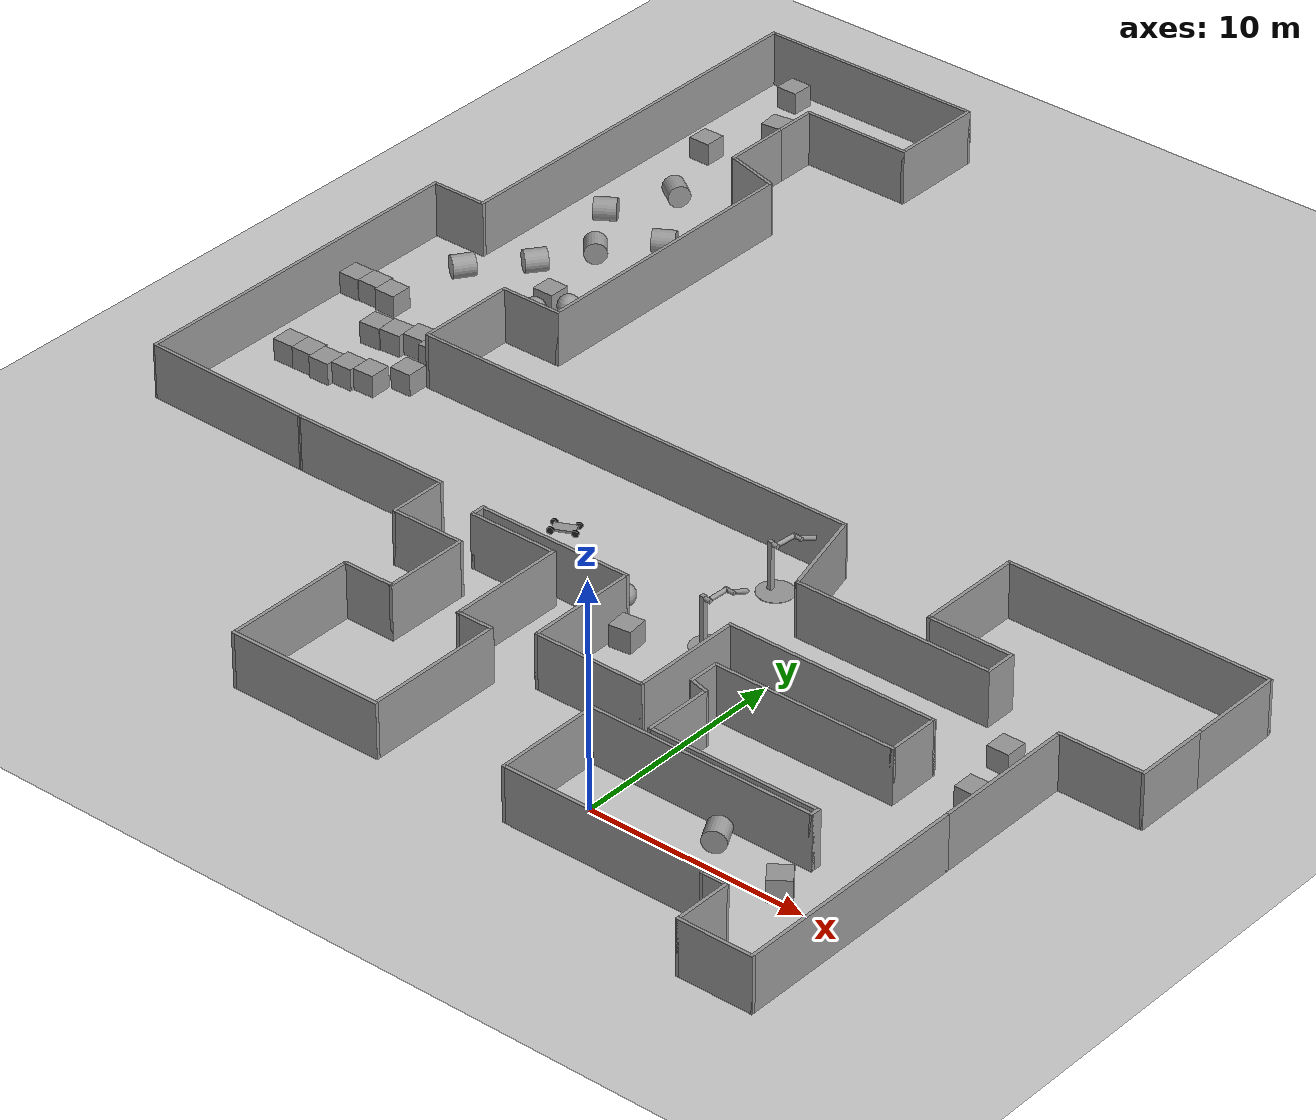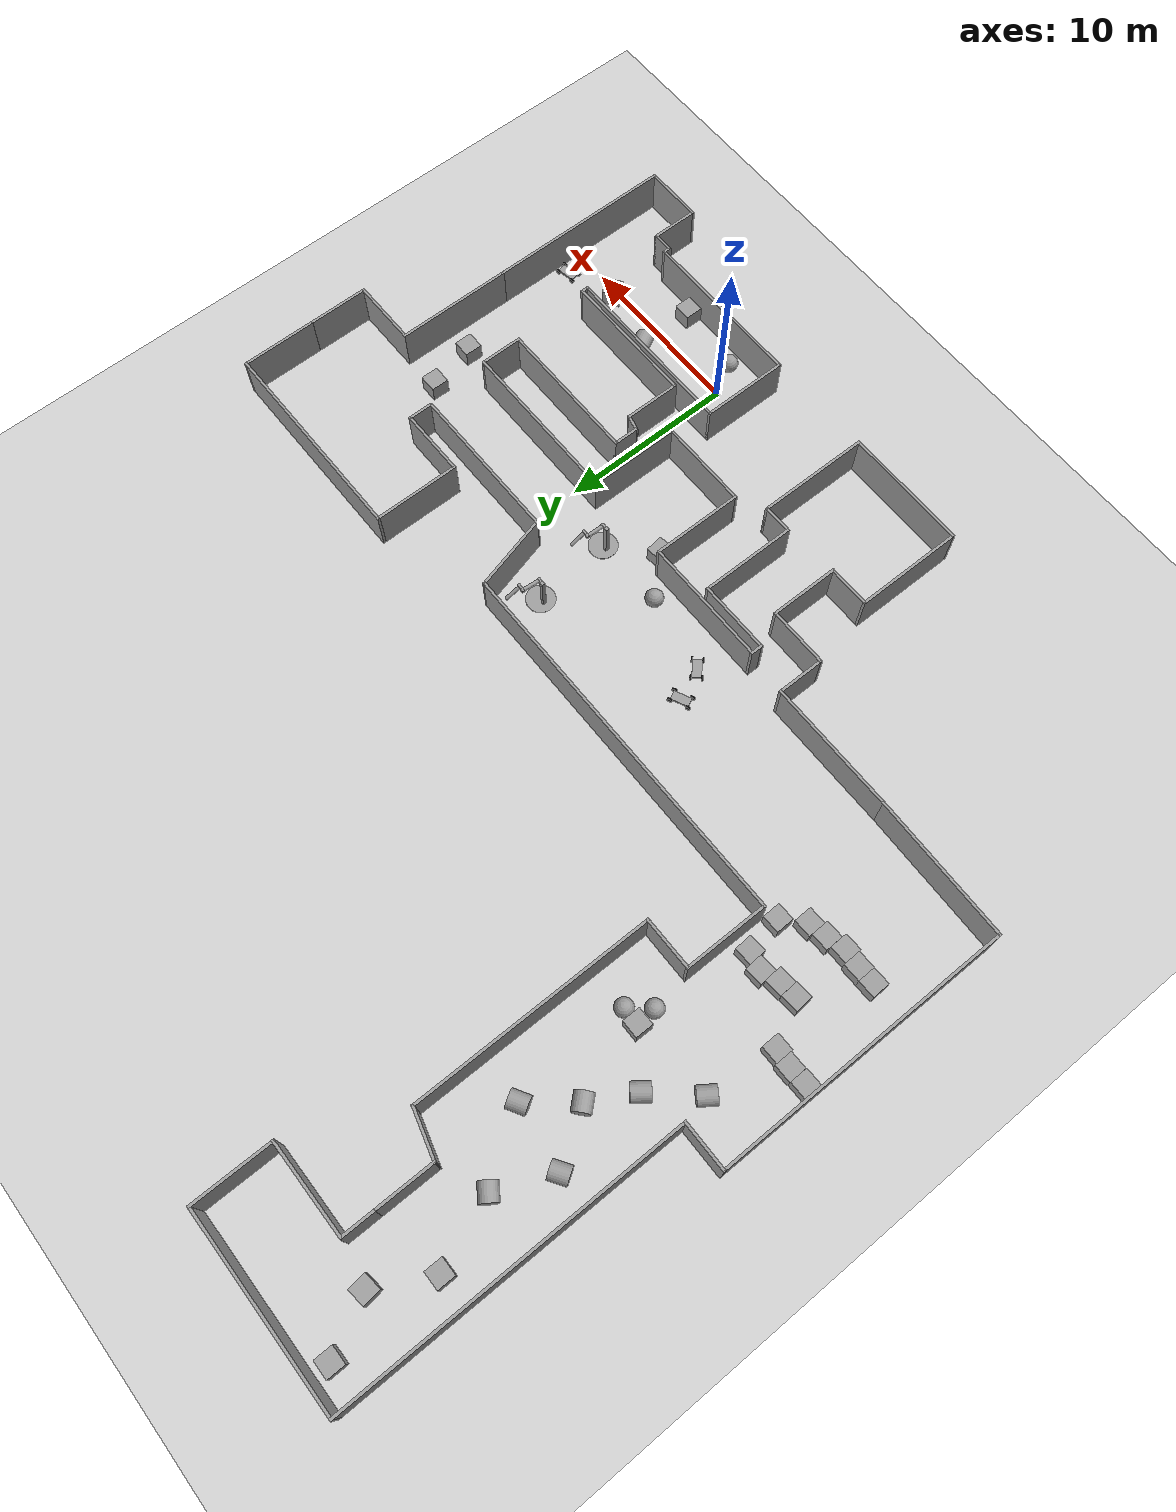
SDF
<sdf version="1.7">
 <world name="default">
  <light name="sun" type="directional">
   <pose>0 0 10 0 -0 0</pose>
   <diffuse>0.8 0.8 0.8 1</diffuse>
   <specular>0.2 0.2 0.2 1</specular>
   <attenuation>
    <range>1000</range>
    <constant>0.9</constant>
    <linear>0.01</linear>
    <quadratic>0.001</quadratic>
   </attenuation>
   <direction>-0.5 0.1 -0.9</direction>
   <spot><inner_angle>0</inner_angle><outer_angle>0</outer_angle><falloff>0</falloff></spot>
  </light>
  <gravity>0 0 0</gravity>
  <magnetic_field>6e-06 2.3e-05 -4.2e-05</magnetic_field>
  <atmosphere type="adiabatic"/>
  <physics type="ode">
   <max_step_size>0.001</max_step_size>
   <real_time_factor>1</real_time_factor>
   <real_time_update_rate>1000</real_time_update_rate>
  </physics>
  <scene><ambient>0.4 0.4 0.4 1</ambient><background>0.7 0.7 0.7 1</background><shadows>1</shadows></scene>
  <plugin name="ros_interface_plugin" filename="librotors_gazebo_ros_interface_plugin.so"/>
  <plugin name="gazebo_ros_state" filename="libgazebo_ros_state.so"/>
  <spherical_coordinates>
   <surface_model>EARTH_WGS84</surface_model>
   <latitude_deg>0</latitude_deg>
   <longitude_deg>0</longitude_deg>
   <elevation>0</elevation>
   <heading_deg>0</heading_deg>
  </spherical_coordinates>
  <model name="ground_plane">
   <static>1</static>
   <link name="link">
    <collision name="collision">
     <geometry><plane><normal>0 0 1</normal><size>100 100</size></plane></geometry>
     <surface><friction><ode><mu>100</mu><mu2>50</mu2></ode></friction></surface>
    </collision>
    <visual name="visual">
     <cast_shadows>0</cast_shadows>
     <geometry><plane><normal>0 0 1</normal><size>100 100</size></plane></geometry>
     <material>
      <script><uri>file://media/materials/scripts/gazebo.material</uri><name>Gazebo/Grey</name></script>
     </material>
    </visual>
   </link>
  </model>
  <model name="complex_env3">
   <pose>-7.7367 20.0281 0 0 -0 0</pose>
   <link name="Wall_1">
    <collision name="Wall_1_Collision">
     <geometry><box><size>11 0.15 2.5</size></box></geometry>
     <pose>0 0 1.25 0 -0 0</pose>
    </collision>
    <visual name="Wall_1_Visual">
     <pose>0 0 1.25 0 -0 0</pose>
     <geometry><box><size>11 0.15 2.5</size></box></geometry>
     <material>
      <script><uri>file://media/materials/scripts/gazebo.material</uri><name>Gazebo/Grey</name></script>
      <ambient>1 1 1 1</ambient>
     </material>
     <meta><layer>0</layer></meta>
    </visual>
    <pose>19.9445 -20.1124 0 0 -0 -1.5708</pose>
   </link>
   <link name="Wall_10">
    <collision name="Wall_10_Collision">
     <geometry><box><size>8 0.15 2.5</size></box></geometry>
     <pose>0 0 1.25 0 -0 0</pose>
    </collision>
    <visual name="Wall_10_Visual">
     <pose>0 0 1.25 0 -0 0</pose>
     <geometry><box><size>8 0.15 2.5</size></box></geometry>
     <material>
      <script><uri>file://media/materials/scripts/gazebo.material</uri><name>Gazebo/Grey</name></script>
      <ambient>1 1 1 1</ambient>
     </material>
     <meta><layer>0</layer></meta>
    </visual>
    <pose>12.3195 -17.3874 0 0 -0 3.14159</pose>
   </link>
   <link name="Wall_11">
    <collision name="Wall_11_Collision">
     <geometry><box><size>3.25 0.15 2.5</size></box></geometry>
     <pose>0 0 1.25 0 -0 0</pose>
    </collision>
    <visual name="Wall_11_Visual">
     <pose>0 0 1.25 0 -0 0</pose>
     <geometry><box><size>3.25 0.15 2.5</size></box></geometry>
     <material>
      <script><uri>file://media/materials/scripts/gazebo.material</uri><name>Gazebo/Grey</name></script>
      <ambient>1 1 1 1</ambient>
     </material>
     <meta><layer>0</layer></meta>
    </visual>
    <pose>8.39449 -15.8374 0 0 -0 1.5708</pose>
   </link>
   <link name="Wall_12">
    <collision name="Wall_12_Collision">
     <geometry><box><size>1 0.15 2.5</size></box></geometry>
     <pose>0 0 1.25 0 -0 0</pose>
    </collision>
    <visual name="Wall_12_Visual">
     <pose>0 0 1.25 0 -0 0</pose>
     <geometry><box><size>1 0.15 2.5</size></box></geometry>
     <material>
      <script><uri>file://media/materials/scripts/gazebo.material</uri><name>Gazebo/Grey</name></script>
      <ambient>1 1 1 1</ambient>
     </material>
     <meta><layer>0</layer></meta>
    </visual>
    <pose>7.98397 -14.1774 0 0 -0 2.87979</pose>
   </link>
   <link name="Wall_13">
    <collision name="Wall_13_Collision">
     <geometry><box><size>1.5 0.15 2.5</size></box></geometry>
     <pose>0 0 1.25 0 -0 0</pose>
    </collision>
    <visual name="Wall_13_Visual">
     <pose>0 0 1.25 0 -0 0</pose>
     <geometry><box><size>1.5 0.15 2.5</size></box></geometry>
     <material>
      <script><uri>file://media/materials/scripts/gazebo.material</uri><name>Gazebo/Grey</name></script>
      <ambient>1 1 1 1</ambient>
     </material>
     <meta><layer>0</layer></meta>
    </visual>
    <pose>7.57345 -13.3924 0 0 -0 1.5708</pose>
   </link>
   <link name="Wall_14">
    <collision name="Wall_14_Collision">
     <geometry><box><size>8.5 0.15 2.5</size></box></geometry>
     <pose>0 0 1.25 0 -0 0</pose>
    </collision>
    <visual name="Wall_14_Visual">
     <pose>0 0 1.25 0 -0 0</pose>
     <geometry><box><size>8.5 0.15 2.5</size></box></geometry>
     <material>
      <script><uri>file://media/materials/scripts/gazebo.material</uri><name>Gazebo/Grey</name></script>
      <ambient>1 1 1 1</ambient>
     </material>
     <meta><layer>0</layer></meta>
    </visual>
    <pose>11.7485 -12.7174 0 0 -0 0</pose>
   </link>
   <link name="Wall_15">
    <collision name="Wall_15_Collision">
     <geometry><box><size>2.5 0.15 2.5</size></box></geometry>
     <pose>0 0 1.25 0 -0 0</pose>
    </collision>
    <visual name="Wall_15_Visual">
     <pose>0 0 1.25 0 -0 0</pose>
     <geometry><box><size>2.5 0.15 2.5</size></box></geometry>
     <material>
      <script><uri>file://media/materials/scripts/gazebo.material</uri><name>Gazebo/Grey</name></script>
      <ambient>1 1 1 1</ambient>
     </material>
     <meta><layer>0</layer></meta>
    </visual>
    <pose>15.9235 -11.5424 0 0 -0 1.5708</pose>
   </link>
   <link name="Wall_16">
    <collision name="Wall_16_Collision">
     <geometry><box><size>9.75 0.15 2.5</size></box></geometry>
     <pose>0 0 1.25 0 -0 0</pose>
    </collision>
    <visual name="Wall_16_Visual">
     <pose>0 0 1.25 0 -0 0</pose>
     <geometry><box><size>9.75 0.15 2.5</size></box></geometry>
     <material>
      <script><uri>file://media/materials/scripts/gazebo.material</uri><name>Gazebo/Grey</name></script>
      <ambient>1 1 1 1</ambient>
     </material>
     <meta><layer>0</layer></meta>
    </visual>
    <pose>11.1235 -10.3674 0 0 -0 3.14159</pose>
   </link>
   <link name="Wall_17">
    <collision name="Wall_17_Collision">
     <geometry><box><size>5.25 0.15 2.5</size></box></geometry>
     <pose>0 0 1.25 0 -0 0</pose>
    </collision>
    <visual name="Wall_17_Visual">
     <pose>0 0 1.25 0 -0 0</pose>
     <geometry><box><size>5.25 0.15 2.5</size></box></geometry>
     <material>
      <script><uri>file://media/materials/scripts/gazebo.material</uri><name>Gazebo/Grey</name></script>
      <ambient>1 1 1 1</ambient>
     </material>
     <meta><layer>0</layer></meta>
    </visual>
    <pose>6.32345 -12.9174 0 0 -0 -1.5708</pose>
   </link>
   <link name="Wall_18">
    <collision name="Wall_18_Collision">
     <geometry><box><size>5.25 0.15 2.5</size></box></geometry>
     <pose>0 0 1.25 0 -0 0</pose>
    </collision>
    <visual name="Wall_18_Visual">
     <pose>0 0 1.25 0 -0 0</pose>
     <geometry><box><size>5.25 0.15 2.5</size></box></geometry>
     <material>
      <script><uri>file://media/materials/scripts/gazebo.material</uri><name>Gazebo/Grey</name></script>
      <ambient>1 1 1 1</ambient>
     </material>
     <meta><layer>0</layer></meta>
    </visual>
    <pose>3.77345 -15.4674 0 0 -0 3.14159</pose>
   </link>
   <link name="Wall_19">
    <collision name="Wall_19_Collision">
     <geometry><box><size>5.25 0.15 2.5</size></box></geometry>
     <pose>0 0 1.25 0 -0 0</pose>
    </collision>
    <visual name="Wall_19_Visual">
     <pose>0 0 1.25 0 -0 0</pose>
     <geometry><box><size>5.25 0.15 2.5</size></box></geometry>
     <material>
      <script><uri>file://media/materials/scripts/gazebo.material</uri><name>Gazebo/Grey</name></script>
      <ambient>1 1 1 1</ambient>
     </material>
     <meta><layer>0</layer></meta>
    </visual>
    <pose>1.22345 -12.9174 0 0 -0 1.5708</pose>
   </link>
   <link name="Wall_2">
    <collision name="Wall_2_Collision">
     <geometry><box><size>3.5 0.15 2.5</size></box></geometry>
     <pose>0 0 1.25 0 -0 0</pose>
    </collision>
    <visual name="Wall_2_Visual">
     <pose>0 0 1.25 0 -0 0</pose>
     <geometry><box><size>3.5 0.15 2.5</size></box></geometry>
     <material>
      <script><uri>file://media/materials/scripts/gazebo.material</uri><name>Gazebo/Grey</name></script>
      <ambient>1 1 1 1</ambient>
     </material>
     <meta><layer>0</layer></meta>
    </visual>
    <pose>18.2695 -25.5374 0 0 -0 3.14159</pose>
   </link>
   <link name="Wall_20">
    <collision name="Wall_20_Collision">
     <geometry><box><size>7.25 0.15 2.5</size></box></geometry>
     <pose>0 0 1.25 0 -0 0</pose>
    </collision>
    <visual name="Wall_20_Visual">
     <pose>0 0 1.25 0 -0 0</pose>
     <geometry><box><size>7.25 0.15 2.5</size></box></geometry>
     <material>
      <script><uri>file://media/materials/scripts/gazebo.material</uri><name>Gazebo/Grey</name></script>
      <ambient>1 1 1 1</ambient>
     </material>
     <meta><layer>0</layer></meta>
    </visual>
    <pose>-2.32655 -10.3674 0 0 -0 3.14159</pose>
   </link>
   <link name="Wall_22">
    <collision name="Wall_22_Collision">
     <geometry><box><size>4.21482 0.15 2.5</size></box></geometry>
     <pose>0 0 1.25 0 -0 0</pose>
    </collision>
    <visual name="Wall_22_Visual">
     <pose>0 0 1.25 0 -0 0</pose>
     <geometry><box><size>4.21482 0.15 2.5</size></box></geometry>
     <material>
      <script><uri>file://media/materials/scripts/gazebo.material</uri><name>Gazebo/Grey</name></script>
      <ambient>1 1 1 1</ambient>
     </material>
     <meta><layer>0</layer></meta>
    </visual>
    <pose>-3.96425 -10.9469 0 0 -0 0</pose>
   </link>
   <link name="Wall_23">
    <collision name="Wall_23_Collision">
     <geometry><box><size>5.5 0.15 2.5</size></box></geometry>
     <pose>0 0 1.25 0 -0 0</pose>
    </collision>
    <visual name="Wall_23_Visual">
     <pose>0 0 1.25 0 -0 0</pose>
     <geometry><box><size>5.5 0.15 2.5</size></box></geometry>
     <material>
      <script><uri>file://media/materials/scripts/gazebo.material</uri><name>Gazebo/Grey</name></script>
      <ambient>1 1 1 1</ambient>
     </material>
     <meta><layer>0</layer></meta>
    </visual>
    <pose>-1.93184 -13.6219 0 0 -0 -1.5708</pose>
   </link>
   <link name="Wall_24">
    <collision name="Wall_24_Collision">
     <geometry><box><size>1.75 0.15 2.5</size></box></geometry>
     <pose>0 0 1.25 0 -0 0</pose>
    </collision>
    <visual name="Wall_24_Visual">
     <pose>0 0 1.25 0 -0 0</pose>
     <geometry><box><size>1.75 0.15 2.5</size></box></geometry>
     <material>
      <script><uri>file://media/materials/scripts/gazebo.material</uri><name>Gazebo/Grey</name></script>
      <ambient>1 1 1 1</ambient>
     </material>
     <meta><layer>0</layer></meta>
    </visual>
    <pose>-1.13184 -16.2969 0 0 -0 0</pose>
   </link>
   <link name="Wall_25">
    <collision name="Wall_25_Collision">
     <geometry><box><size>6.5 0.15 2.5</size></box></geometry>
     <pose>0 0 1.25 0 -0 0</pose>
    </collision>
    <visual name="Wall_25_Visual">
     <pose>0 0 1.25 0 -0 0</pose>
     <geometry><box><size>6.5 0.15 2.5</size></box></geometry>
     <material>
      <script><uri>file://media/materials/scripts/gazebo.material</uri><name>Gazebo/Grey</name></script>
      <ambient>1 1 1 1</ambient>
     </material>
     <meta><layer>0</layer></meta>
    </visual>
    <pose>-0.331841 -19.4719 0 0 -0 -1.5708</pose>
   </link>
   <link name="Wall_26">
    <collision name="Wall_26_Collision">
     <geometry><box><size>7.25 0.15 2.5</size></box></geometry>
     <pose>0 0 1.25 0 -0 0</pose>
    </collision>
    <visual name="Wall_26_Visual">
     <pose>0 0 1.25 0 -0 0</pose>
     <geometry><box><size>7.25 0.15 2.5</size></box></geometry>
     <material>
      <script><uri>file://media/materials/scripts/gazebo.material</uri><name>Gazebo/Grey</name></script>
      <ambient>1 1 1 1</ambient>
     </material>
     <meta><layer>0</layer></meta>
    </visual>
    <pose>-3.88184 -22.6469 0 0 -0 3.14159</pose>
   </link>
   <link name="Wall_27">
    <collision name="Wall_27_Collision">
     <geometry><box><size>6.25 0.15 2.5</size></box></geometry>
     <pose>0 0 1.25 0 -0 0</pose>
    </collision>
    <visual name="Wall_27_Visual">
     <pose>0 0 1.25 0 -0 0</pose>
     <geometry><box><size>6.25 0.15 2.5</size></box></geometry>
     <material>
      <script><uri>file://media/materials/scripts/gazebo.material</uri><name>Gazebo/Grey</name></script>
      <ambient>1 1 1 1</ambient>
     </material>
     <meta><layer>0</layer></meta>
    </visual>
    <pose>-7.43184 -19.5969 0 0 -0 1.5708</pose>
   </link>
   <link name="Wall_28">
    <collision name="Wall_28_Collision">
     <geometry><box><size>2.5 0.15 2.5</size></box></geometry>
     <pose>0 0 1.25 0 -0 0</pose>
    </collision>
    <visual name="Wall_28_Visual">
     <pose>0 0 1.25 0 -0 0</pose>
     <geometry><box><size>2.5 0.15 2.5</size></box></geometry>
     <material>
      <script><uri>file://media/materials/scripts/gazebo.material</uri><name>Gazebo/Grey</name></script>
      <ambient>1 1 1 1</ambient>
     </material>
     <meta><layer>0</layer></meta>
    </visual>
    <pose>-6.25684 -16.5469 0 0 -0 0</pose>
   </link>
   <link name="Wall_29">
    <collision name="Wall_29_Collision">
     <geometry><box><size>4 0.15 2.5</size></box></geometry>
     <pose>0 0 1.25 0 -0 0</pose>
    </collision>
    <visual name="Wall_29_Visual">
     <pose>0 0 1.25 0 -0 0</pose>
     <geometry><box><size>4 0.15 2.5</size></box></geometry>
     <material>
      <script><uri>file://media/materials/scripts/gazebo.material</uri><name>Gazebo/Grey</name></script>
      <ambient>1 1 1 1</ambient>
     </material>
     <meta><layer>0</layer></meta>
    </visual>
    <pose>-5.08184 -14.6219 0 0 -0 1.5708</pose>
   </link>
   <link name="Wall_3">
    <collision name="Wall_3_Collision">
     <geometry><box><size>2.75 0.15 2.5</size></box></geometry>
     <pose>0 0 1.25 0 -0 0</pose>
    </collision>
    <visual name="Wall_3_Visual">
     <pose>0 0 1.25 0 -0 0</pose>
     <geometry><box><size>2.75 0.15 2.5</size></box></geometry>
     <material>
      <script><uri>file://media/materials/scripts/gazebo.material</uri><name>Gazebo/Grey</name></script>
      <ambient>1 1 1 1</ambient>
     </material>
     <meta><layer>0</layer></meta>
    </visual>
    <pose>16.5945 -24.2374 0 0 -0 1.5708</pose>
   </link>
   <link name="Wall_30">
    <collision name="Wall_30_Collision">
     <geometry><box><size>3.5 0.15 2.5</size></box></geometry>
     <pose>0 0 1.25 0 -0 0</pose>
    </collision>
    <visual name="Wall_30_Visual">
     <pose>0 0 1.25 0 -0 0</pose>
     <geometry><box><size>3.5 0.15 2.5</size></box></geometry>
     <material>
      <script><uri>file://media/materials/scripts/gazebo.material</uri><name>Gazebo/Grey</name></script>
      <ambient>1 1 1 1</ambient>
     </material>
     <meta><layer>0</layer></meta>
    </visual>
    <pose>-6.75684 -12.6969 0 0 -0 3.14159</pose>
   </link>
   <link name="Wall_31">
    <collision name="Wall_31_Collision">
     <geometry><box><size>2.75 0.15 2.5</size></box></geometry>
     <pose>0 0 1.25 0 -0 0</pose>
    </collision>
    <visual name="Wall_31_Visual">
     <pose>0 0 1.25 0 -0 0</pose>
     <geometry><box><size>2.75 0.15 2.5</size></box></geometry>
     <material>
      <script><uri>file://media/materials/scripts/gazebo.material</uri><name>Gazebo/Grey</name></script>
      <ambient>1 1 1 1</ambient>
     </material>
     <meta><layer>0</layer></meta>
    </visual>
    <pose>-8.43184 -11.3969 0 0 -0 1.5708</pose>
   </link>
   <link name="Wall_32">
    <collision name="Wall_32_Collision">
     <geometry><box><size>7.5 0.15 2.5</size></box></geometry>
     <pose>0 0 1.25 0 -0 0</pose>
    </collision>
    <visual name="Wall_32_Visual">
     <pose>0 0 1.25 0 -0 0</pose>
     <geometry><box><size>7.5 0.15 2.5</size></box></geometry>
     <material>
      <script><uri>file://media/materials/scripts/gazebo.material</uri><name>Gazebo/Grey</name></script>
      <ambient>1 1 1 1</ambient>
     </material>
     <meta><layer>0</layer></meta>
    </visual>
    <pose>-12.1068 -10.0969 0 0 -0 3.14159</pose>
   </link>
   <link name="Wall_4">
    <collision name="Wall_4_Collision">
     <geometry><box><size>1.25 0.15 2.5</size></box></geometry>
     <pose>0 0 1.25 0 -0 0</pose>
    </collision>
    <visual name="Wall_4_Visual">
     <pose>0 0 1.25 0 -0 0</pose>
     <geometry><box><size>1.25 0.15 2.5</size></box></geometry>
     <material>
      <script><uri>file://media/materials/scripts/gazebo.material</uri><name>Gazebo/Grey</name></script>
      <ambient>1 1 1 1</ambient>
     </material>
     <meta><layer>0</layer></meta>
    </visual>
    <pose>16.0445 -22.9374 0 0 -0 3.14159</pose>
   </link>
   <link name="Wall_41">
    <collision name="Wall_41_Collision">
     <geometry><box><size>0.75 0.15 2.5</size></box></geometry>
     <pose>0 0 1.25 0 -0 0</pose>
    </collision>
    <visual name="Wall_41_Visual">
     <pose>0 0 1.25 0 -0 0</pose>
     <geometry><box><size>0.75 0.15 2.5</size></box></geometry>
     <material>
      <script><uri>file://media/materials/scripts/gazebo.material</uri><name>Gazebo/Grey</name></script>
      <ambient>1 1 1 1</ambient>
     </material>
     <meta><layer>0</layer></meta>
    </visual>
    <pose>-5.99666 -10.6469 0 0 -0 1.5708</pose>
   </link>
   <link name="Wall_43">
    <collision name="Wall_43_Collision">
     <geometry><box><size>6.75 0.15 2.5</size></box></geometry>
     <pose>0 0 1.25 0 -0 0</pose>
    </collision>
    <visual name="Wall_43_Visual">
     <pose>0 0 1.25 0 -0 0</pose>
     <geometry><box><size>6.75 0.15 2.5</size></box></geometry>
     <material>
      <script><uri>file://media/materials/scripts/gazebo.material</uri><name>Gazebo/Grey</name></script>
      <ambient>1 1 1 1</ambient>
     </material>
     <meta><layer>0</layer></meta>
    </visual>
    <pose>19.9445 -11.3874 0 0 -0 1.5708</pose>
   </link>
   <link name="Wall_44">
    <collision name="Wall_44_Collision">
     <geometry><box><size>4 0.15 2.5</size></box></geometry>
     <pose>0 0 1.25 0 -0 0</pose>
    </collision>
    <visual name="Wall_44_Visual">
     <pose>0 0 1.25 0 -0 0</pose>
     <geometry><box><size>4 0.15 2.5</size></box></geometry>
     <material>
      <script><uri>file://media/materials/scripts/gazebo.material</uri><name>Gazebo/Grey</name></script>
      <ambient>1 1 1 1</ambient>
     </material>
     <meta><layer>0</layer></meta>
    </visual>
    <pose>21.8695 -8.08735 0 0 -0 0</pose>
   </link>
   <link name="Wall_45">
    <collision name="Wall_45_Collision">
     <geometry><box><size>3.5 0.15 2.5</size></box></geometry>
     <pose>0 0 1.25 0 -0 0</pose>
    </collision>
    <visual name="Wall_45_Visual">
     <pose>0 0 1.25 0 -0 0</pose>
     <geometry><box><size>3.5 0.15 2.5</size></box></geometry>
     <material>
      <script><uri>file://media/materials/scripts/gazebo.material</uri><name>Gazebo/Grey</name></script>
      <ambient>1 1 1 1</ambient>
     </material>
     <meta><layer>0</layer></meta>
    </visual>
    <pose>23.7945 -6.41235 0 0 -0 1.5708</pose>
   </link>
   <link name="Wall_46">
    <collision name="Wall_46_Collision">
     <geometry><box><size>4.5 0.15 2.5</size></box></geometry>
     <pose>0 0 1.25 0 -0 0</pose>
    </collision>
    <visual name="Wall_46_Visual">
     <pose>0 0 1.25 0 -0 0</pose>
     <geometry><box><size>4.5 0.15 2.5</size></box></geometry>
     <material>
      <script><uri>file://media/materials/scripts/gazebo.material</uri><name>Gazebo/Grey</name></script>
      <ambient>1 1 1 1</ambient>
     </material>
     <meta><layer>0</layer></meta>
    </visual>
    <pose>23.7945 -2.56235 0 0 -0 1.5708</pose>
   </link>
   <link name="Wall_47">
    <collision name="Wall_47_Collision">
     <geometry><box><size>12.25 0.15 2.5</size></box></geometry>
     <pose>0 0 1.25 0 -0 0</pose>
    </collision>
    <visual name="Wall_47_Visual">
     <pose>0 0 1.25 0 -0 0</pose>
     <geometry><box><size>12.25 0.15 2.5</size></box></geometry>
     <material>
      <script><uri>file://media/materials/scripts/gazebo.material</uri><name>Gazebo/Grey</name></script>
      <ambient>1 1 1 1</ambient>
     </material>
     <meta><layer>0</layer></meta>
    </visual>
    <pose>17.7445 -0.387354 0 0 -0 3.14159</pose>
   </link>
   <link name="Wall_48">
    <collision name="Wall_48_Collision">
     <geometry><box><size>5 0.15 2.5</size></box></geometry>
     <pose>0 0 1.25 0 -0 0</pose>
    </collision>
    <visual name="Wall_48_Visual">
     <pose>0 0 1.25 0 -0 0</pose>
     <geometry><box><size>5 0.15 2.5</size></box></geometry>
     <material>
      <script><uri>file://media/materials/scripts/gazebo.material</uri><name>Gazebo/Grey</name></script>
      <ambient>1 1 1 1</ambient>
     </material>
     <meta><layer>0</layer></meta>
    </visual>
    <pose>11.6945 -2.81235 0 0 -0 -1.5708</pose>
   </link>
   <link name="Wall_49">
    <collision name="Wall_49_Collision">
     <geometry><box><size>4 0.15 2.5</size></box></geometry>
     <pose>0 0 1.25 0 -0 0</pose>
    </collision>
    <visual name="Wall_49_Visual">
     <pose>0 0 1.25 0 -0 0</pose>
     <geometry><box><size>4 0.15 2.5</size></box></geometry>
     <material>
      <script><uri>file://media/materials/scripts/gazebo.material</uri><name>Gazebo/Grey</name></script>
      <ambient>1 1 1 1</ambient>
     </material>
     <meta><layer>0</layer></meta>
    </visual>
    <pose>13.6195 -5.23735 0 0 -0 0</pose>
   </link>
   <link name="Wall_5">
    <collision name="Wall_5_Collision">
     <geometry><box><size>0.5 0.15 2.5</size></box></geometry>
     <pose>0 0 1.25 0 -0 0</pose>
    </collision>
    <visual name="Wall_5_Visual">
     <pose>0 0 1.25 0 -0 0</pose>
     <geometry><box><size>0.5 0.15 2.5</size></box></geometry>
     <material>
      <script><uri>file://media/materials/scripts/gazebo.material</uri><name>Gazebo/Grey</name></script>
      <ambient>1 1 1 1</ambient>
     </material>
     <meta><layer>0</layer></meta>
    </visual>
    <pose>15.4945 -22.7624 0 0 -0 1.5708</pose>
   </link>
   <link name="Wall_50">
    <collision name="Wall_50_Collision">
     <geometry><box><size>1.5 0.15 2.5</size></box></geometry>
     <pose>0 0 1.25 0 -0 0</pose>
    </collision>
    <visual name="Wall_50_Visual">
     <pose>0 0 1.25 0 -0 0</pose>
     <geometry><box><size>1.5 0.15 2.5</size></box></geometry>
     <material>
      <script><uri>file://media/materials/scripts/gazebo.material</uri><name>Gazebo/Grey</name></script>
      <ambient>1 1 1 1</ambient>
     </material>
     <meta><layer>0</layer></meta>
    </visual>
    <pose>15.5445 -5.91235 0 0 -0 -1.5708</pose>
   </link>
   <link name="Wall_51">
    <collision name="Wall_51_Collision">
     <geometry><box><size>9.25 0.15 2.5</size></box></geometry>
     <pose>0 0 1.25 0 -0 0</pose>
    </collision>
    <visual name="Wall_51_Visual">
     <pose>0 0 1.25 0 -0 0</pose>
     <geometry><box><size>9.25 0.15 2.5</size></box></geometry>
     <material>
      <script><uri>file://media/materials/scripts/gazebo.material</uri><name>Gazebo/Grey</name></script>
      <ambient>1 1 1 1</ambient>
     </material>
     <meta><layer>0</layer></meta>
    </visual>
    <pose>10.9945 -6.58735 0 0 -0 3.14159</pose>
   </link>
   <link name="Wall_52">
    <collision name="Wall_52_Collision">
     <geometry><box><size>4.5 0.15 2.5</size></box></geometry>
     <pose>0 0 1.25 0 -0 0</pose>
    </collision>
    <visual name="Wall_52_Visual">
     <pose>0 0 1.25 0 -0 0</pose>
     <geometry><box><size>4.5 0.15 2.5</size></box></geometry>
     <material>
      <script><uri>file://media/materials/scripts/gazebo.material</uri><name>Gazebo/Grey</name></script>
      <ambient>1 1 1 1</ambient>
     </material>
     <meta><layer>0</layer></meta>
    </visual>
    <pose>5.88156 -4.48646 0 0 -0 1.8326</pose>
   </link>
   <link name="Wall_53">
    <collision name="Wall_53_Collision">
     <geometry><box><size>21.5 0.15 2.5</size></box></geometry>
     <pose>0 0 1.25 0 -0 0</pose>
    </collision>
    <visual name="Wall_53_Visual">
     <pose>0 0 1.25 0 -0 0</pose>
     <geometry><box><size>21.5 0.15 2.5</size></box></geometry>
     <material>
      <script><uri>file://media/materials/scripts/gazebo.material</uri><name>Gazebo/Grey</name></script>
      <ambient>1 1 1 1</ambient>
     </material>
     <meta><layer>0</layer></meta>
    </visual>
    <pose>-5.35638 -2.38558 0 0 -0 3.14159</pose>
   </link>
   <link name="Wall_54">
    <collision name="Wall_54_Collision">
     <geometry><box><size>4.75 0.15 2.5</size></box></geometry>
     <pose>0 0 1.25 0 -0 0</pose>
    </collision>
    <visual name="Wall_54_Visual">
     <pose>0 0 1.25 0 -0 0</pose>
     <geometry><box><size>4.75 0.15 2.5</size></box></geometry>
     <material>
      <script><uri>file://media/materials/scripts/gazebo.material</uri><name>Gazebo/Grey</name></script>
      <ambient>1 1 1 1</ambient>
     </material>
     <meta><layer>0</layer></meta>
    </visual>
    <pose>-16.0314 -0.085575 0 0 -0 1.5708</pose>
   </link>
   <link name="Wall_55">
    <collision name="Wall_55_Collision">
     <geometry><box><size>3 0.15 2.5</size></box></geometry>
     <pose>0 0 1.25 0 -0 0</pose>
    </collision>
    <visual name="Wall_55_Visual">
     <pose>0 0 1.25 0 -0 0</pose>
     <geometry><box><size>3 0.15 2.5</size></box></geometry>
     <material>
      <script><uri>file://media/materials/scripts/gazebo.material</uri><name>Gazebo/Grey</name></script>
      <ambient>1 1 1 1</ambient>
     </material>
     <meta><layer>0</layer></meta>
    </visual>
    <pose>-14.6064 2.21442 0 0 -0 0</pose>
   </link>
   <link name="Wall_56">
    <collision name="Wall_56_Collision">
     <geometry><box><size>13.5 0.15 2.5</size></box></geometry>
     <pose>0 0 1.25 0 -0 0</pose>
    </collision>
    <visual name="Wall_56_Visual">
     <pose>0 0 1.25 0 -0 0</pose>
     <geometry><box><size>13.5 0.15 2.5</size></box></geometry>
     <material>
      <script><uri>file://media/materials/scripts/gazebo.material</uri><name>Gazebo/Grey</name></script>
      <ambient>1 1 1 1</ambient>
     </material>
     <meta><layer>0</layer></meta>
    </visual>
    <pose>-13.1814 8.88942 0 0 -0 1.5708</pose>
   </link>
   <link name="Wall_57">
    <collision name="Wall_57_Collision">
     <geometry><box><size>2.75 0.15 2.5</size></box></geometry>
     <pose>0 0 1.25 0 -0 0</pose>
    </collision>
    <visual name="Wall_57_Visual">
     <pose>0 0 1.25 0 -0 0</pose>
     <geometry><box><size>2.75 0.15 2.5</size></box></geometry>
     <material>
      <script><uri>file://media/materials/scripts/gazebo.material</uri><name>Gazebo/Grey</name></script>
      <ambient>1 1 1 1</ambient>
     </material>
     <meta><layer>0</layer></meta>
    </visual>
    <pose>-14.4371 15.9009 0 0 -0 2.87979</pose>
   </link>
   <link name="Wall_58">
    <collision name="Wall_58_Collision">
     <geometry><box><size>3.25 0.15 2.5</size></box></geometry>
     <pose>0 0 1.25 0 -0 0</pose>
    </collision>
    <visual name="Wall_58_Visual">
     <pose>0 0 1.25 0 -0 0</pose>
     <geometry><box><size>3.25 0.15 2.5</size></box></geometry>
     <material>
      <script><uri>file://media/materials/scripts/gazebo.material</uri><name>Gazebo/Grey</name></script>
      <ambient>1 1 1 1</ambient>
     </material>
     <meta><layer>0</layer></meta>
    </visual>
    <pose>-15.6928 17.7874 0 0 -0 1.5708</pose>
   </link>
   <link name="Wall_59">
    <collision name="Wall_59_Collision">
     <geometry><box><size>2 0.15 2.5</size></box></geometry>
     <pose>0 0 1.25 0 -0 0</pose>
    </collision>
    <visual name="Wall_59_Visual">
     <pose>0 0 1.25 0 -0 0</pose>
     <geometry><box><size>2 0.15 2.5</size></box></geometry>
     <material>
      <script><uri>file://media/materials/scripts/gazebo.material</uri><name>Gazebo/Grey</name></script>
      <ambient>1 1 1 1</ambient>
     </material>
     <meta><layer>0</layer></meta>
    </visual>
    <pose>-15.6928 20.2624 0 0 -0 1.5708</pose>
   </link>
   <link name="Wall_6">
    <collision name="Wall_6_Collision">
     <geometry><box><size>9.75 0.15 2.5</size></box></geometry>
     <pose>0 0 1.25 0 -0 0</pose>
    </collision>
    <visual name="Wall_6_Visual">
     <pose>0 0 1.25 0 -0 0</pose>
     <geometry><box><size>9.75 0.15 2.5</size></box></geometry>
     <material>
      <script><uri>file://media/materials/scripts/gazebo.material</uri><name>Gazebo/Grey</name></script>
      <ambient>1 1 1 1</ambient>
     </material>
     <meta><layer>0</layer></meta>
    </visual>
    <pose>10.6945 -22.5874 0 0 -0 3.14159</pose>
   </link>
   <link name="Wall_60">
    <collision name="Wall_60_Collision">
     <geometry><box><size>5.25 0.15 2.5</size></box></geometry>
     <pose>0 0 1.25 0 -0 0</pose>
    </collision>
    <visual name="Wall_60_Visual">
     <pose>0 0 1.25 0 -0 0</pose>
     <geometry><box><size>5.25 0.15 2.5</size></box></geometry>
     <material>
      <script><uri>file://media/materials/scripts/gazebo.material</uri><name>Gazebo/Grey</name></script>
      <ambient>1 1 1 1</ambient>
     </material>
     <meta><layer>0</layer></meta>
    </visual>
    <pose>-13.1428 21.1874 0 0 -0 0</pose>
   </link>
   <link name="Wall_61">
    <collision name="Wall_61_Collision">
     <geometry><box><size>4.5 0.15 2.5</size></box></geometry>
     <pose>0 0 1.25 0 -0 0</pose>
    </collision>
    <visual name="Wall_61_Visual">
     <pose>0 0 1.25 0 -0 0</pose>
     <geometry><box><size>4.5 0.15 2.5</size></box></geometry>
     <material>
      <script><uri>file://media/materials/scripts/gazebo.material</uri><name>Gazebo/Grey</name></script>
      <ambient>1 1 1 1</ambient>
     </material>
     <meta><layer>0</layer></meta>
    </visual>
    <pose>-10.5928 23.3624 0 0 -0 1.5708</pose>
   </link>
   <link name="Wall_62">
    <collision name="Wall_62_Collision">
     <geometry><box><size>10.75 0.15 2.5</size></box></geometry>
     <pose>0 0 1.25 0 -0 0</pose>
    </collision>
    <visual name="Wall_62_Visual">
     <pose>0 0 1.25 0 -0 0</pose>
     <geometry><box><size>10.75 0.15 2.5</size></box></geometry>
     <material>
      <script><uri>file://media/materials/scripts/gazebo.material</uri><name>Gazebo/Grey</name></script>
      <ambient>1 1 1 1</ambient>
     </material>
     <meta><layer>0</layer></meta>
    </visual>
    <pose>-15.8928 25.5374 0 0 -0 3.14159</pose>
   </link>
   <link name="Wall_63">
    <collision name="Wall_63_Collision">
     <geometry><box><size>19 0.15 2.5</size></box></geometry>
     <pose>0 0 1.25 0 -0 0</pose>
    </collision>
    <visual name="Wall_63_Visual">
     <pose>0 0 1.25 0 -0 0</pose>
     <geometry><box><size>19 0.15 2.5</size></box></geometry>
     <material>
      <script><uri>file://media/materials/scripts/gazebo.material</uri><name>Gazebo/Grey</name></script>
      <ambient>1 1 1 1</ambient>
     </material>
     <meta><layer>0</layer></meta>
    </visual>
    <pose>-21.1928 16.1124 0 0 -0 -1.5708</pose>
   </link>
   <link name="Wall_64">
    <collision name="Wall_64_Collision">
     <geometry><box><size>2.75 0.15 2.5</size></box></geometry>
     <pose>0 0 1.25 0 -0 0</pose>
    </collision>
    <visual name="Wall_64_Visual">
     <pose>0 0 1.25 0 -0 0</pose>
     <geometry><box><size>2.75 0.15 2.5</size></box></geometry>
     <material>
      <script><uri>file://media/materials/scripts/gazebo.material</uri><name>Gazebo/Grey</name></script>
      <ambient>1 1 1 1</ambient>
     </material>
     <meta><layer>0</layer></meta>
    </visual>
    <pose>-22.4928 6.68735 0 0 -0 3.14159</pose>
   </link>
   <link name="Wall_65">
    <collision name="Wall_65_Collision">
     <geometry><box><size>16.75 0.15 2.5</size></box></geometry>
     <pose>0 0 1.25 0 -0 0</pose>
    </collision>
    <visual name="Wall_65_Visual">
     <pose>0 0 1.25 0 -0 0</pose>
     <geometry><box><size>16.75 0.15 2.5</size></box></geometry>
     <material>
      <script><uri>file://media/materials/scripts/gazebo.material</uri><name>Gazebo/Grey</name></script>
      <ambient>1 1 1 1</ambient>
     </material>
     <meta><layer>0</layer></meta>
    </visual>
    <pose>-23.7928 -1.61265 0 0 -0 -1.5708</pose>
   </link>
   <link name="Wall_66">
    <collision name="Wall_66_Collision">
     <geometry><box><size>8.16306 0.15 2.5</size></box></geometry>
     <pose>0 0 1.25 0 -0 0</pose>
    </collision>
    <visual name="Wall_66_Visual">
     <pose>0 0 1.25 0 -0 0</pose>
     <geometry><box><size>8.16306 0.15 2.5</size></box></geometry>
     <material>
      <script><uri>file://media/materials/scripts/gazebo.material</uri><name>Gazebo/Grey</name></script>
      <ambient>1 1 1 1</ambient>
     </material>
     <meta><layer>0</layer></meta>
    </visual>
    <pose>-19.7873 -10.0048 0 0 -0 -0.022998</pose>
   </link>
   <link name="Wall_7">
    <collision name="Wall_7_Collision">
     <geometry><box><size>5 0.15 2.5</size></box></geometry>
     <pose>0 0 1.25 0 -0 0</pose>
    </collision>
    <visual name="Wall_7_Visual">
     <pose>0 0 1.25 0 -0 0</pose>
     <geometry><box><size>5 0.15 2.5</size></box></geometry>
     <material>
      <script><uri>file://media/materials/scripts/gazebo.material</uri><name>Gazebo/Grey</name></script>
      <ambient>1 1 1 1</ambient>
     </material>
     <meta><layer>0</layer></meta>
    </visual>
    <pose>5.89449 -20.1624 0 0 -0 1.5708</pose>
   </link>
   <link name="Wall_8">
    <collision name="Wall_8_Collision">
     <geometry><box><size>10.5 0.15 2.5</size></box></geometry>
     <pose>0 0 1.25 0 -0 0</pose>
    </collision>
    <visual name="Wall_8_Visual">
     <pose>0 0 1.25 0 -0 0</pose>
     <geometry><box><size>10.5 0.15 2.5</size></box></geometry>
     <material>
      <script><uri>file://media/materials/scripts/gazebo.material</uri><name>Gazebo/Grey</name></script>
      <ambient>1 1 1 1</ambient>
     </material>
     <meta><layer>0</layer></meta>
    </visual>
    <pose>11.0695 -17.7374 0 0 -0 0</pose>
   </link>
   <link name="Wall_9">
    <collision name="Wall_9_Collision">
     <geometry><box><size>0.5 0.15 2.5</size></box></geometry>
     <pose>0 0 1.25 0 -0 0</pose>
    </collision>
    <visual name="Wall_9_Visual">
     <pose>0 0 1.25 0 -0 0</pose>
     <geometry><box><size>0.5 0.15 2.5</size></box></geometry>
     <material>
      <script><uri>file://media/materials/scripts/gazebo.material</uri><name>Gazebo/Grey</name></script>
      <ambient>1 1 1 1</ambient>
     </material>
     <meta><layer>0</layer></meta>
    </visual>
    <pose>16.2445 -17.5624 0 0 -0 1.5708</pose>
   </link>
   <static>1</static>
  </model>
  <model name="unit_box">
   <pose>8.58499 0.438001 0.5 0 -0 0.641361</pose>
   <link name="link">
    <inertial>
     <mass>1</mass>
     <inertia>
      <ixx>0.166667</ixx>
      <ixy>0</ixy>
      <ixz>0</ixz>
      <iyy>0.166667</iyy>
      <iyz>0</iyz>
      <izz>0.166667</izz>
     </inertia>
    </inertial>
    <collision name="collision"><geometry><box><size>1 1 1</size></box></geometry></collision>
    <visual name="visual">
     <geometry><box><size>1 1 1</size></box></geometry>
     <material>
      <script><name>Gazebo/Grey</name><uri>file://media/materials/scripts/gazebo.material</uri></script>
     </material>
    </visual>
   </link>
  </model>
  <model name="unit_box_0">
   <pose>4.85833 -1.98403 0.499995 0 -1e-05 0.000539</pose>
   <link name="link">
    <inertial>
     <mass>1</mass>
     <inertia>
      <ixx>0.166667</ixx>
      <ixy>0</ixy>
      <ixz>0</ixz>
      <iyy>0.166667</iyy>
      <iyz>0</iyz>
      <izz>0.166667</izz>
     </inertia>
    </inertial>
    <collision name="collision"><geometry><box><size>1 1 1</size></box></geometry></collision>
    <visual name="visual">
     <geometry><box><size>1 1 1</size></box></geometry>
     <material>
      <script><name>Gazebo/Grey</name><uri>file://media/materials/scripts/gazebo.material</uri></script>
     </material>
    </visual>
   </link>
  </model>
  <model name="unit_cylinder">
   <pose>4.95476 1.27157 0.499996 -1.5708 0.000138 0.48701</pose>
   <link name="link">
    <inertial>
     <mass>1</mass>
     <inertia><ixx>0.145833</ixx><ixy>0</ixy><ixz>0</ixz><iyy>0.145833</iyy><iyz>0</iyz><izz>0.125</izz></inertia>
    </inertial>
    <collision name="collision">
     <geometry><cylinder><radius>0.5</radius><length>1</length></cylinder></geometry>
    </collision>
    <visual name="visual">
     <geometry><cylinder><radius>0.5</radius><length>1</length></cylinder></geometry>
     <material>
      <script><name>Gazebo/Grey</name><uri>file://media/materials/scripts/gazebo.material</uri></script>
     </material>
    </visual>
   </link>
  </model>
  <model name="unit_sphere">
   <pose>0.887488 -1.57296 0.5 0 -0 0</pose>
   <link name="link">
    <inertial>
     <mass>1</mass>
     <inertia><ixx>0.1</ixx><ixy>0</ixy><ixz>0</ixz><iyy>0.1</iyy><iyz>0</iyz><izz>0.1</izz></inertia>
    </inertial>
    <collision name="collision"><geometry><sphere><radius>0.5</radius></sphere></geometry></collision>
    <visual name="visual">
     <geometry><sphere><radius>0.5</radius></sphere></geometry>
     <material>
      <script><name>Gazebo/Grey</name><uri>file://media/materials/scripts/gazebo.material</uri></script>
     </material>
    </visual>
   </link>
  </model>
  <model name="cart_front_steer">
   <link name="chassis">
    <pose>0 0 0.15 0 -0 0</pose>
    <inertial>
     <pose>0.1 0 0 0 -0 0</pose>
     <mass>10</mass>
     <inertia>
      <ixx>0.216667</ixx>
      <iyy>0.841667</iyy>
      <izz>1.04167</izz>
      <ixy>0</ixy>
      <ixz>0</ixz>
      <iyz>0</iyz>
     </inertia>
    </inertial>
    <collision name="collision"><geometry><box><size>1 0.5 0.1</size></box></geometry></collision>
    <visual name="visual">
     <geometry><box><size>1 0.5 0.1</size></box></geometry>
     <material>
      <script><uri>file://media/materials/scripts/gazebo.material</uri><name>Gazebo/Grey</name></script>
     </material>
    </visual>
   </link>
   <link name="wheel_front_left">
    <pose>0.5 0.298 0.15 -1.5708 -0.087266 0</pose>
    <inertial>
     <mass>0.5</mass>
     <inertia>
      <ixx>0.00307917</ixx>
      <iyy>0.00307917</iyy>
      <izz>0.005625</izz>
      <ixy>0</ixy>
      <ixz>0</ixz>
      <iyz>0</iyz>
     </inertia>
    </inertial>
    <collision name="collision">
     <geometry><cylinder><radius>0.15</radius><length>0.08</length></cylinder></geometry>
    </collision>
    <visual name="visual">
     <geometry><cylinder><radius>0.15</radius><length>0.08</length></cylinder></geometry>
     <material>
      <script><uri>file://media/materials/scripts/gazebo.material</uri><name>Gazebo/Black</name></script>
     </material>
    </visual>
   </link>
   <joint name="wheel_front_left_steer_spin" type="universal">
    <parent>chassis</parent>
    <child>wheel_front_left</child>
    <axis>
     <xyz>0 -1 0</xyz>
     <limit><lower>-0.610865</lower><upper>0.610865</upper></limit>
     <dynamics><spring_reference>0</spring_reference><spring_stiffness>0</spring_stiffness></dynamics>
    </axis>
    <axis2>
     <xyz>0 0 1</xyz>
     <limit><upper>1e+16</upper><lower>-1e+16</lower></limit>
     <dynamics><spring_reference>0</spring_reference><spring_stiffness>0</spring_stiffness></dynamics>
    </axis2>
   </joint>
   <link name="wheel_front_right">
    <pose>0.5 -0.298 0.15 -1.5708 -0.087266 0</pose>
    <inertial>
     <mass>0.5</mass>
     <inertia>
      <ixx>0.00307917</ixx>
      <iyy>0.00307917</iyy>
      <izz>0.005625</izz>
      <ixy>0</ixy>
      <ixz>0</ixz>
      <iyz>0</iyz>
     </inertia>
    </inertial>
    <collision name="collision">
     <geometry><cylinder><radius>0.15</radius><length>0.08</length></cylinder></geometry>
    </collision>
    <visual name="visual">
     <geometry><cylinder><radius>0.15</radius><length>0.08</length></cylinder></geometry>
     <material>
      <script><uri>file://media/materials/scripts/gazebo.material</uri><name>Gazebo/Black</name></script>
     </material>
    </visual>
   </link>
   <joint name="wheel_front_right_steer_spin" type="universal">
    <parent>chassis</parent>
    <child>wheel_front_right</child>
    <axis>
     <xyz>0 -1 0</xyz>
     <limit><lower>-0.610865</lower><upper>0.610865</upper></limit>
     <dynamics><spring_reference>0</spring_reference><spring_stiffness>0</spring_stiffness></dynamics>
    </axis>
    <axis2>
     <xyz>0 0 1</xyz>
     <limit><upper>1e+16</upper><lower>-1e+16</lower></limit>
     <dynamics><spring_reference>0</spring_reference><spring_stiffness>0</spring_stiffness></dynamics>
    </axis2>
   </joint>
   <link name="wheel_rear_left">
    <pose>-0.5 0.298 0.15 -1.5708 0 0</pose>
    <inertial>
     <mass>0.5</mass>
     <inertia>
      <ixx>0.00307917</ixx>
      <iyy>0.00307917</iyy>
      <izz>0.005625</izz>
      <ixy>0</ixy>
      <ixz>0</ixz>
      <iyz>0</iyz>
     </inertia>
    </inertial>
    <collision name="collision">
     <geometry><cylinder><radius>0.15</radius><length>0.08</length></cylinder></geometry>
    </collision>
    <visual name="visual">
     <geometry><cylinder><radius>0.15</radius><length>0.08</length></cylinder></geometry>
     <material>
      <script><uri>file://media/materials/scripts/gazebo.material</uri><name>Gazebo/Black</name></script>
     </material>
    </visual>
   </link>
   <joint name="wheel_rear_left_spin" type="revolute">
    <parent>chassis</parent>
    <child>wheel_rear_left</child>
    <axis>
     <xyz>0 0 1</xyz>
     <limit><lower>-1e+16</lower><upper>1e+16</upper></limit>
     <dynamics><spring_reference>0</spring_reference><spring_stiffness>0</spring_stiffness></dynamics>
    </axis>
   </joint>
   <link name="wheel_rear_right">
    <pose>-0.5 -0.298 0.15 -1.5708 0 0</pose>
    <inertial>
     <mass>0.5</mass>
     <inertia>
      <ixx>0.00307917</ixx>
      <iyy>0.00307917</iyy>
      <izz>0.005625</izz>
      <ixy>0</ixy>
      <ixz>0</ixz>
      <iyz>0</iyz>
     </inertia>
    </inertial>
    <collision name="collision">
     <geometry><cylinder><radius>0.15</radius><length>0.08</length></cylinder></geometry>
    </collision>
    <visual name="visual">
     <geometry><cylinder><radius>0.15</radius><length>0.08</length></cylinder></geometry>
     <material>
      <script><uri>file://media/materials/scripts/gazebo.material</uri><name>Gazebo/Black</name></script>
     </material>
    </visual>
   </link>
   <joint name="wheel_rear_right_spin" type="revolute">
    <parent>chassis</parent>
    <child>wheel_rear_right</child>
    <axis>
     <xyz>0 0 1</xyz>
     <limit><lower>-1e+16</lower><upper>1e+16</upper></limit>
     <dynamics><spring_reference>0</spring_reference><spring_stiffness>0</spring_stiffness></dynamics>
    </axis>
   </joint>
   <pose>11.4248 1.37036 -2e-06 -1.6e-05 -1e-06 0.198064</pose>
  </model>
  <model name="double_pendulum_with_base_2">
   <link name="base">
    <inertial>
     <mass>100</mass>
     <inertia><ixx>1</ixx><ixy>0</ixy><ixz>0</ixz><iyy>1</iyy><iyz>0</iyz><izz>1</izz></inertia>
    </inertial>
    <visual name="vis_plate_on_ground">
     <pose>0 0 0.01 0 -0 0</pose>
     <geometry><cylinder><radius>0.8</radius><length>0.02</length></cylinder></geometry>
     <material>
      <script><uri>file://media/materials/scripts/gazebo.material</uri><name>Gazebo/Grey</name></script>
     </material>
    </visual>
    <visual name="vis_pole">
     <pose>-0.275 0 1.1 0 -0 0</pose>
     <geometry><box><size>0.2 0.2 2.2</size></box></geometry>
     <material>
      <script><uri>file://media/materials/scripts/gazebo.material</uri><name>Gazebo/Grey</name></script>
     </material>
    </visual>
    <collision name="col_plate_on_ground">
     <pose>0 0 0.01 0 -0 0</pose>
     <geometry><cylinder><radius>0.8</radius><length>0.02</length></cylinder></geometry>
    </collision>
    <collision name="col_pole">
     <pose>-0.275 0 1.1 0 -0 0</pose>
     <geometry><box><size>0.2 0.2 2.2</size></box></geometry>
    </collision>
   </link>
   <link name="upper_link">
    <pose>0 0 2.1 -1.5708 0 0</pose>
    <inertial>
     <pose>0 0 0.5 0 -0 0</pose>
     <inertia><ixx>1</ixx><ixy>0</ixy><ixz>0</ixz><iyy>1</iyy><iyz>0</iyz><izz>1</izz></inertia>
     <mass>1</mass>
    </inertial>
    <visual name="vis_upper_joint">
     <pose>-0.05 0 0 3.14159 1.57079 3.14159</pose>
     <geometry><cylinder><radius>0.1</radius><length>0.3</length></cylinder></geometry>
     <material>
      <script><uri>file://media/materials/scripts/gazebo.material</uri><name>Gazebo/Grey</name></script>
     </material>
    </visual>
    <visual name="vis_lower_joint">
     <pose>0 0 1 3.14159 1.57079 3.14159</pose>
     <geometry><cylinder><radius>0.1</radius><length>0.2</length></cylinder></geometry>
     <material>
      <script><uri>file://media/materials/scripts/gazebo.material</uri><name>Gazebo/Grey</name></script>
     </material>
    </visual>
    <visual name="vis_cylinder">
     <pose>0 0 0.5 0 -0 0</pose>
     <geometry><cylinder><radius>0.1</radius><length>0.9</length></cylinder></geometry>
     <material>
      <script><uri>file://media/materials/scripts/gazebo.material</uri><name>Gazebo/Grey</name></script>
     </material>
    </visual>
    <collision name="col_upper_joint">
     <pose>-0.05 0 0 3.14159 1.57079 3.14159</pose>
     <geometry><cylinder><radius>0.1</radius><length>0.3</length></cylinder></geometry>
    </collision>
    <collision name="col_lower_joint">
     <pose>0 0 1 3.14159 1.57079 3.14159</pose>
     <geometry><cylinder><radius>0.1</radius><length>0.2</length></cylinder></geometry>
    </collision>
    <collision name="col_cylinder">
     <pose>0 0 0.5 0 -0 0</pose>
     <geometry><cylinder><radius>0.1</radius><length>0.9</length></cylinder></geometry>
    </collision>
   </link>
   <link name="lower_link">
    <pose>0.25 1 2.1 -2 0 0</pose>
    <inertial>
     <pose>0 0 0.5 0 -0 0</pose>
     <inertia><ixx>1</ixx><ixy>0</ixy><ixz>0</ixz><iyy>1</iyy><iyz>0</iyz><izz>1</izz></inertia>
     <mass>1</mass>
    </inertial>
    <visual name="vis_lower_joint">
     <pose>0 0 0 3.14159 1.57079 3.14159</pose>
     <geometry><cylinder><radius>0.08</radius><length>0.3</length></cylinder></geometry>
     <material>
      <script><uri>file://media/materials/scripts/gazebo.material</uri><name>Gazebo/Grey</name></script>
     </material>
    </visual>
    <visual name="vis_cylinder">
     <pose>0 0 0.5 0 -0 0</pose>
     <geometry><cylinder><radius>0.1</radius><length>0.9</length></cylinder></geometry>
     <material>
      <script><uri>file://media/materials/scripts/gazebo.material</uri><name>Gazebo/Grey</name></script>
     </material>
    </visual>
    <collision name="col_lower_joint">
     <pose>0 0 0 3.14159 1.57079 3.14159</pose>
     <geometry><cylinder><radius>0.08</radius><length>0.3</length></cylinder></geometry>
    </collision>
    <collision name="col_cylinder">
     <pose>0 0 0.5 0 -0 0</pose>
     <geometry><cylinder><radius>0.1</radius><length>0.9</length></cylinder></geometry>
    </collision>
   </link>
   <joint name="upper_joint" type="revolute">
    <parent>base</parent>
    <child>upper_link</child>
    <axis>
     <xyz>1 0 0</xyz>
     <limit><lower>-1e+16</lower><upper>1e+16</upper></limit>
     <dynamics><spring_reference>0</spring_reference><spring_stiffness>0</spring_stiffness></dynamics>
    </axis>
   </joint>
   <joint name="lower_joint" type="revolute">
    <parent>upper_link</parent>
    <child>lower_link</child>
    <axis>
     <xyz>1 0 0</xyz>
     <limit><lower>-1e+16</lower><upper>1e+16</upper></limit>
     <dynamics><spring_reference>0</spring_reference><spring_stiffness>0</spring_stiffness></dynamics>
    </axis>
   </joint>
   <pose>-3.84296 15.2744 -0 0 1e-06 -0.077361</pose>
  </model>
  <model name="double_pendulum_with_base_3">
   <link name="base">
    <inertial>
     <mass>100</mass>
     <inertia><ixx>1</ixx><ixy>0</ixy><ixz>0</ixz><iyy>1</iyy><iyz>0</iyz><izz>1</izz></inertia>
    </inertial>
    <visual name="vis_plate_on_ground">
     <pose>0 0 0.01 0 -0 0</pose>
     <geometry><cylinder><radius>0.8</radius><length>0.02</length></cylinder></geometry>
     <material>
      <script><uri>file://media/materials/scripts/gazebo.material</uri><name>Gazebo/Grey</name></script>
     </material>
    </visual>
    <visual name="vis_pole">
     <pose>-0.275 0 1.1 0 -0 0</pose>
     <geometry><box><size>0.2 0.2 2.2</size></box></geometry>
     <material>
      <script><uri>file://media/materials/scripts/gazebo.material</uri><name>Gazebo/Grey</name></script>
     </material>
    </visual>
    <collision name="col_plate_on_ground">
     <pose>0 0 0.01 0 -0 0</pose>
     <geometry><cylinder><radius>0.8</radius><length>0.02</length></cylinder></geometry>
    </collision>
    <collision name="col_pole">
     <pose>-0.275 0 1.1 0 -0 0</pose>
     <geometry><box><size>0.2 0.2 2.2</size></box></geometry>
    </collision>
   </link>
   <link name="upper_link">
    <pose>0 0 2.1 -1.5708 0 0</pose>
    <inertial>
     <pose>0 0 0.5 0 -0 0</pose>
     <inertia><ixx>1</ixx><ixy>0</ixy><ixz>0</ixz><iyy>1</iyy><iyz>0</iyz><izz>1</izz></inertia>
     <mass>1</mass>
    </inertial>
    <visual name="vis_upper_joint">
     <pose>-0.05 0 0 3.14159 1.57079 3.14159</pose>
     <geometry><cylinder><radius>0.1</radius><length>0.3</length></cylinder></geometry>
     <material>
      <script><uri>file://media/materials/scripts/gazebo.material</uri><name>Gazebo/Grey</name></script>
     </material>
    </visual>
    <visual name="vis_lower_joint">
     <pose>0 0 1 3.14159 1.57079 3.14159</pose>
     <geometry><cylinder><radius>0.1</radius><length>0.2</length></cylinder></geometry>
     <material>
      <script><uri>file://media/materials/scripts/gazebo.material</uri><name>Gazebo/Grey</name></script>
     </material>
    </visual>
    <visual name="vis_cylinder">
     <pose>0 0 0.5 0 -0 0</pose>
     <geometry><cylinder><radius>0.1</radius><length>0.9</length></cylinder></geometry>
     <material>
      <script><uri>file://media/materials/scripts/gazebo.material</uri><name>Gazebo/Grey</name></script>
     </material>
    </visual>
    <collision name="col_upper_joint">
     <pose>-0.05 0 0 3.14159 1.57079 3.14159</pose>
     <geometry><cylinder><radius>0.1</radius><length>0.3</length></cylinder></geometry>
    </collision>
    <collision name="col_lower_joint">
     <pose>0 0 1 3.14159 1.57079 3.14159</pose>
     <geometry><cylinder><radius>0.1</radius><length>0.2</length></cylinder></geometry>
    </collision>
    <collision name="col_cylinder">
     <pose>0 0 0.5 0 -0 0</pose>
     <geometry><cylinder><radius>0.1</radius><length>0.9</length></cylinder></geometry>
    </collision>
   </link>
   <link name="lower_link">
    <pose>0.25 1 2.1 -2 0 0</pose>
    <inertial>
     <pose>0 0 0.5 0 -0 0</pose>
     <inertia><ixx>1</ixx><ixy>0</ixy><ixz>0</ixz><iyy>1</iyy><iyz>0</iyz><izz>1</izz></inertia>
     <mass>1</mass>
    </inertial>
    <visual name="vis_lower_joint">
     <pose>0 0 0 3.14159 1.57079 3.14159</pose>
     <geometry><cylinder><radius>0.08</radius><length>0.3</length></cylinder></geometry>
     <material>
      <script><uri>file://media/materials/scripts/gazebo.material</uri><name>Gazebo/Grey</name></script>
     </material>
    </visual>
    <visual name="vis_cylinder">
     <pose>0 0 0.5 0 -0 0</pose>
     <geometry><cylinder><radius>0.1</radius><length>0.9</length></cylinder></geometry>
     <material>
      <script><uri>file://media/materials/scripts/gazebo.material</uri><name>Gazebo/Grey</name></script>
     </material>
    </visual>
    <collision name="col_lower_joint">
     <pose>0 0 0 3.14159 1.57079 3.14159</pose>
     <geometry><cylinder><radius>0.08</radius><length>0.3</length></cylinder></geometry>
    </collision>
    <collision name="col_cylinder">
     <pose>0 0 0.5 0 -0 0</pose>
     <geometry><cylinder><radius>0.1</radius><length>0.9</length></cylinder></geometry>
    </collision>
   </link>
   <joint name="upper_joint" type="revolute">
    <parent>base</parent>
    <child>upper_link</child>
    <axis>
     <xyz>1 0 0</xyz>
     <limit><lower>-1e+16</lower><upper>1e+16</upper></limit>
     <dynamics><spring_reference>0</spring_reference><spring_stiffness>0</spring_stiffness></dynamics>
    </axis>
   </joint>
   <joint name="lower_joint" type="revolute">
    <parent>upper_link</parent>
    <child>lower_link</child>
    <axis>
     <xyz>1 0 0</xyz>
     <limit><lower>-1e+16</lower><upper>1e+16</upper></limit>
     <dynamics><spring_reference>0</spring_reference><spring_stiffness>0</spring_stiffness></dynamics>
    </axis>
   </joint>
   <pose>-3.41869 10.7915 0 0 0 -0.0373</pose>
  </model>
  <model name="unit_box_2">
   <pose>-5.87193 8.92366 0.499995 -0 1e-05 0.122908</pose>
   <link name="link">
    <inertial>
     <mass>1</mass>
     <inertia>
      <ixx>0.166667</ixx>
      <ixy>0</ixy>
      <ixz>0</ixz>
      <iyy>0.166667</iyy>
      <iyz>0</iyz>
      <izz>0.166667</izz>
     </inertia>
    </inertial>
    <collision name="collision"><geometry><box><size>1 1 1</size></box></geometry></collision>
    <visual name="visual">
     <geometry><box><size>1 1 1</size></box></geometry>
     <material>
      <script><name>Gazebo/Grey</name><uri>file://media/materials/scripts/gazebo.material</uri></script>
     </material>
    </visual>
   </link>
  </model>
  <model name="unit_sphere_0">
   <pose>-7.65578 10.8174 0.5 0 -0 0</pose>
   <link name="link">
    <inertial>
     <mass>1</mass>
     <inertia><ixx>0.1</ixx><ixy>0</ixy><ixz>0</ixz><iyy>0.1</iyy><iyz>0</iyz><izz>0.1</izz></inertia>
    </inertial>
    <collision name="collision"><geometry><sphere><radius>0.5</radius></sphere></geometry></collision>
    <visual name="visual">
     <geometry><sphere><radius>0.5</radius></sphere></geometry>
     <material>
      <script><name>Gazebo/Grey</name><uri>file://media/materials/scripts/gazebo.material</uri></script>
     </material>
    </visual>
   </link>
  </model>
  <model name="unit_box_4">
   <pose>-29.466 15.6921 0.499995 -1e-05 -0 0.020412</pose>
   <link name="link">
    <inertial>
     <mass>1</mass>
     <inertia>
      <ixx>0.166667</ixx>
      <ixy>0</ixy>
      <ixz>0</ixz>
      <iyy>0.166667</iyy>
      <iyz>0</iyz>
      <izz>0.166667</izz>
     </inertia>
    </inertial>
    <collision name="collision"><geometry><box><size>1 1 1</size></box></geometry></collision>
    <visual name="visual">
     <geometry><box><size>1 1 1</size></box></geometry>
     <material>
      <script><name>Gazebo/Grey</name><uri>file://media/materials/scripts/gazebo.material</uri></script>
     </material>
    </visual>
   </link>
  </model>
  <model name="unit_box_5">
   <pose>-28.4661 15.7075 0.5 0 -0 0.020412</pose>
   <link name="link">
    <inertial>
     <mass>1</mass>
     <inertia>
      <ixx>0.166667</ixx>
      <ixy>0</ixy>
      <ixz>0</ixz>
      <iyy>0.166667</iyy>
      <iyz>0</iyz>
      <izz>0.166667</izz>
     </inertia>
    </inertial>
    <collision name="collision"><geometry><box><size>1 1 1</size></box></geometry></collision>
    <visual name="visual">
     <geometry><box><size>1 1 1</size></box></geometry>
     <material>
      <script><name>Gazebo/Grey</name><uri>file://media/materials/scripts/gazebo.material</uri></script>
     </material>
    </visual>
   </link>
  </model>
  <model name="unit_box_6">
   <pose>-27.4639 15.6221 0.5 0 -0 0.020525</pose>
   <link name="link">
    <inertial>
     <mass>1</mass>
     <inertia>
      <ixx>0.166667</ixx>
      <ixy>0</ixy>
      <ixz>0</ixz>
      <iyy>0.166667</iyy>
      <iyz>0</iyz>
      <izz>0.166667</izz>
     </inertia>
    </inertial>
    <collision name="collision"><geometry><box><size>1 1 1</size></box></geometry></collision>
    <visual name="visual">
     <geometry><box><size>1 1 1</size></box></geometry>
     <material>
      <script><name>Gazebo/Grey</name><uri>file://media/materials/scripts/gazebo.material</uri></script>
     </material>
    </visual>
   </link>
  </model>
  <model name="unit_box_7">
   <pose>-24.3975 17.1188 0.5 0 -0 0.024781</pose>
   <link name="link">
    <inertial>
     <mass>1</mass>
     <inertia>
      <ixx>0.166667</ixx>
      <ixy>0</ixy>
      <ixz>0</ixz>
      <iyy>0.166667</iyy>
      <iyz>0</iyz>
      <izz>0.166667</izz>
     </inertia>
    </inertial>
    <collision name="collision"><geometry><box><size>1 1 1</size></box></geometry></collision>
    <visual name="visual">
     <geometry><box><size>1 1 1</size></box></geometry>
     <material>
      <script><name>Gazebo/Grey</name><uri>file://media/materials/scripts/gazebo.material</uri></script>
     </material>
    </visual>
   </link>
  </model>
  <model name="unit_box_8">
   <pose>-25.4725 16.0922 0.5 0 -0 0.021424</pose>
   <link name="link">
    <inertial>
     <mass>1</mass>
     <inertia>
      <ixx>0.166667</ixx>
      <ixy>0</ixy>
      <ixz>0</ixz>
      <iyy>0.166667</iyy>
      <iyz>0</iyz>
      <izz>0.166667</izz>
     </inertia>
    </inertial>
    <collision name="collision"><geometry><box><size>1 1 1</size></box></geometry></collision>
    <visual name="visual">
     <geometry><box><size>1 1 1</size></box></geometry>
     <material>
      <script><name>Gazebo/Grey</name><uri>file://media/materials/scripts/gazebo.material</uri></script>
     </material>
    </visual>
   </link>
  </model>
  <model name="unit_box_9">
   <pose>-26.4692 15.8946 0.5 0 -0 0.020705</pose>
   <link name="link">
    <inertial>
     <mass>1</mass>
     <inertia>
      <ixx>0.166667</ixx>
      <ixy>0</ixy>
      <ixz>0</ixz>
      <iyy>0.166667</iyy>
      <iyz>0</iyz>
      <izz>0.166667</izz>
     </inertia>
    </inertial>
    <collision name="collision"><geometry><box><size>1 1 1</size></box></geometry></collision>
    <visual name="visual">
     <geometry><box><size>1 1 1</size></box></geometry>
     <material>
      <script><name>Gazebo/Grey</name><uri>file://media/materials/scripts/gazebo.material</uri></script>
     </material>
    </visual>
   </link>
  </model>
  <model name="unit_box_10">
   <pose>-30.9397 21.2031 0.5 0 -0 0.009314</pose>
   <link name="link">
    <inertial>
     <mass>1</mass>
     <inertia>
      <ixx>0.166667</ixx>
      <ixy>0</ixy>
      <ixz>0</ixz>
      <iyy>0.166667</iyy>
      <iyz>0</iyz>
      <izz>0.166667</izz>
     </inertia>
    </inertial>
    <collision name="collision"><geometry><box><size>1 1 1</size></box></geometry></collision>
    <visual name="visual">
     <geometry><box><size>1 1 1</size></box></geometry>
     <material>
      <script><name>Gazebo/Grey</name><uri>file://media/materials/scripts/gazebo.material</uri></script>
     </material>
    </visual>
   </link>
  </model>
  <model name="unit_box_11">
   <pose>-29.9394 21.2525 0.5 0 -0 0.009495</pose>
   <link name="link">
    <inertial>
     <mass>1</mass>
     <inertia>
      <ixx>0.166667</ixx>
      <ixy>0</ixy>
      <ixz>0</ixz>
      <iyy>0.166667</iyy>
      <iyz>0</iyz>
      <izz>0.166667</izz>
     </inertia>
    </inertial>
    <collision name="collision"><geometry><box><size>1 1 1</size></box></geometry></collision>
    <visual name="visual">
     <geometry><box><size>1 1 1</size></box></geometry>
     <material>
      <script><name>Gazebo/Grey</name><uri>file://media/materials/scripts/gazebo.material</uri></script>
     </material>
    </visual>
   </link>
  </model>
  <model name="unit_box_12">
   <pose>-28.9381 21.1597 0.5 0 -0 0.009902</pose>
   <link name="link">
    <inertial>
     <mass>1</mass>
     <inertia>
      <ixx>0.166667</ixx>
      <ixy>0</ixy>
      <ixz>0</ixz>
      <iyy>0.166667</iyy>
      <iyz>0</iyz>
      <izz>0.166667</izz>
     </inertia>
    </inertial>
    <collision name="collision"><geometry><box><size>1 1 1</size></box></geometry></collision>
    <visual name="visual">
     <geometry><box><size>1 1 1</size></box></geometry>
     <material>
      <script><name>Gazebo/Grey</name><uri>file://media/materials/scripts/gazebo.material</uri></script>
     </material>
    </visual>
   </link>
  </model>
  <model name="unit_box_13">
   <pose>-27.7219 18.9013 0.5 0 -0 0.064363</pose>
   <link name="link">
    <inertial>
     <mass>1</mass>
     <inertia>
      <ixx>0.166667</ixx>
      <ixy>0</ixy>
      <ixz>0</ixz>
      <iyy>0.166667</iyy>
      <iyz>0</iyz>
      <izz>0.166667</izz>
     </inertia>
    </inertial>
    <collision name="collision"><geometry><box><size>1 1 1</size></box></geometry></collision>
    <visual name="visual">
     <geometry><box><size>1 1 1</size></box></geometry>
     <material>
      <script><name>Gazebo/Grey</name><uri>file://media/materials/scripts/gazebo.material</uri></script>
     </material>
    </visual>
   </link>
  </model>
  <model name="unit_box_14">
   <pose>-26.7267 19.0169 0.499995 0 1e-05 0.064981</pose>
   <link name="link">
    <inertial>
     <mass>1</mass>
     <inertia>
      <ixx>0.166667</ixx>
      <ixy>0</ixy>
      <ixz>0</ixz>
      <iyy>0.166667</iyy>
      <iyz>0</iyz>
      <izz>0.166667</izz>
     </inertia>
    </inertial>
    <collision name="collision"><geometry><box><size>1 1 1</size></box></geometry></collision>
    <visual name="visual">
     <geometry><box><size>1 1 1</size></box></geometry>
     <material>
      <script><name>Gazebo/Grey</name><uri>file://media/materials/scripts/gazebo.material</uri></script>
     </material>
    </visual>
   </link>
  </model>
  <model name="unit_box_15">
   <pose>-25.747 19.3641 0.5 0 -0 0.064685</pose>
   <link name="link">
    <inertial>
     <mass>1</mass>
     <inertia>
      <ixx>0.166667</ixx>
      <ixy>0</ixy>
      <ixz>0</ixz>
      <iyy>0.166667</iyy>
      <iyz>0</iyz>
      <izz>0.166667</izz>
     </inertia>
    </inertial>
    <collision name="collision"><geometry><box><size>1 1 1</size></box></geometry></collision>
    <visual name="visual">
     <geometry><box><size>1 1 1</size></box></geometry>
     <material>
      <script><name>Gazebo/Grey</name><uri>file://media/materials/scripts/gazebo.material</uri></script>
     </material>
    </visual>
   </link>
  </model>
  <model name="unit_box_16">
   <pose>-24.7292 19.1355 0.5 0 -0 0.060436</pose>
   <link name="link">
    <inertial>
     <mass>1</mass>
     <inertia>
      <ixx>0.166667</ixx>
      <ixy>0</ixy>
      <ixz>0</ixz>
      <iyy>0.166667</iyy>
      <iyz>0</iyz>
      <izz>0.166667</izz>
     </inertia>
    </inertial>
    <collision name="collision"><geometry><box><size>1 1 1</size></box></geometry></collision>
    <visual name="visual">
     <geometry><box><size>1 1 1</size></box></geometry>
     <material>
      <script><name>Gazebo/Grey</name><uri>file://media/materials/scripts/gazebo.material</uri></script>
     </material>
    </visual>
   </link>
  </model>
  <model name="unit_box_17">
   <pose>-27.0016 44.5815 0.5 -0 -0 -5e-06</pose>
   <link name="link">
    <inertial>
     <mass>1</mass>
     <inertia>
      <ixx>0.166667</ixx>
      <ixy>0</ixy>
      <ixz>0</ixz>
      <iyy>0.166667</iyy>
      <iyz>0</iyz>
      <izz>0.166667</izz>
     </inertia>
    </inertial>
    <collision name="collision"><geometry><box><size>1 1 1</size></box></geometry></collision>
    <visual name="visual">
     <geometry><box><size>1 1 1</size></box></geometry>
     <material>
      <script><name>Gazebo/Grey</name><uri>file://media/materials/scripts/gazebo.material</uri></script>
     </material>
    </visual>
   </link>
  </model>
  <model name="unit_box_18">
   <pose>-25.5631 41.7649 0.499997 0 5e-06 0.12837</pose>
   <link name="link">
    <inertial>
     <mass>1</mass>
     <inertia>
      <ixx>0.166667</ixx>
      <ixy>0</ixy>
      <ixz>0</ixz>
      <iyy>0.166667</iyy>
      <iyz>0</iyz>
      <izz>0.166667</izz>
     </inertia>
    </inertial>
    <collision name="collision"><geometry><box><size>1 1 1</size></box></geometry></collision>
    <visual name="visual">
     <geometry><box><size>1 1 1</size></box></geometry>
     <material>
      <script><name>Gazebo/Grey</name><uri>file://media/materials/scripts/gazebo.material</uri></script>
     </material>
    </visual>
   </link>
  </model>
  <model name="unit_box_19">
   <pose>-27.0831 38.8535 0.5 -0 -0 -5e-06</pose>
   <link name="link">
    <inertial>
     <mass>1</mass>
     <inertia>
      <ixx>0.166667</ixx>
      <ixy>0</ixy>
      <ixz>0</ixz>
      <iyy>0.166667</iyy>
      <iyz>0</iyz>
      <izz>0.166667</izz>
     </inertia>
    </inertial>
    <collision name="collision"><geometry><box><size>1 1 1</size></box></geometry></collision>
    <visual name="visual">
     <geometry><box><size>1 1 1</size></box></geometry>
     <material>
      <script><name>Gazebo/Grey</name><uri>file://media/materials/scripts/gazebo.material</uri></script>
     </material>
    </visual>
   </link>
  </model>
  <model name="unit_cylinder_0">
   <pose>-25.6566 35.1955 0.5 1.57029 -1.57045 -2.16863</pose>
   <link name="link">
    <inertial>
     <mass>1</mass>
     <inertia><ixx>0.145833</ixx><ixy>0</ixy><ixz>0</ixz><iyy>0.145833</iyy><iyz>0</iyz><izz>0.125</izz></inertia>
    </inertial>
    <collision name="collision">
     <geometry><cylinder><radius>0.5</radius><length>1</length></cylinder></geometry>
    </collision>
    <visual name="visual">
     <geometry><cylinder><radius>0.5</radius><length>1</length></cylinder></geometry>
     <material>
      <script><name>Gazebo/Grey</name><uri>file://media/materials/scripts/gazebo.material</uri></script>
     </material>
    </visual>
   </link>
  </model>
  <model name="unit_cylinder_1">
   <pose>-26.9878 32.212 0.5 -1.57072 1.5687 -0.99423</pose>
   <link name="link">
    <inertial>
     <mass>1</mass>
     <inertia><ixx>0.145833</ixx><ixy>0</ixy><ixz>0</ixz><iyy>0.145833</iyy><iyz>0</iyz><izz>0.125</izz></inertia>
    </inertial>
    <collision name="collision">
     <geometry><cylinder><radius>0.5</radius><length>1</length></cylinder></geometry>
    </collision>
    <visual name="visual">
     <geometry><cylinder><radius>0.5</radius><length>1</length></cylinder></geometry>
     <material>
      <script><name>Gazebo/Grey</name><uri>file://media/materials/scripts/gazebo.material</uri></script>
     </material>
    </visual>
   </link>
  </model>
  <model name="unit_cylinder_2">
   <pose>-25.2311 29.5284 0.499995 -1.57704 -1.56928 0.731236</pose>
   <link name="link">
    <inertial>
     <mass>1</mass>
     <inertia><ixx>0.145833</ixx><ixy>0</ixy><ixz>0</ixz><iyy>0.145833</iyy><iyz>0</iyz><izz>0.125</izz></inertia>
    </inertial>
    <collision name="collision">
     <geometry><cylinder><radius>0.5</radius><length>1</length></cylinder></geometry>
    </collision>
    <visual name="visual">
     <geometry><cylinder><radius>0.5</radius><length>1</length></cylinder></geometry>
     <material>
      <script><name>Gazebo/Grey</name><uri>file://media/materials/scripts/gazebo.material</uri></script>
     </material>
    </visual>
   </link>
  </model>
  <model name="unit_cylinder_3">
   <pose>-26.5012 27.1904 0.5 -1.57039 1.57034 -0.648526</pose>
   <link name="link">
    <inertial>
     <mass>1</mass>
     <inertia><ixx>0.145833</ixx><ixy>0</ixy><ixz>0</ixz><iyy>0.145833</iyy><iyz>0</iyz><izz>0.125</izz></inertia>
    </inertial>
    <collision name="collision">
     <geometry><cylinder><radius>0.5</radius><length>1</length></cylinder></geometry>
    </collision>
    <visual name="visual">
     <geometry><cylinder><radius>0.5</radius><length>1</length></cylinder></geometry>
     <material>
      <script><name>Gazebo/Grey</name><uri>file://media/materials/scripts/gazebo.material</uri></script>
     </material>
    </visual>
   </link>
  </model>
  <model name="unit_cylinder_4">
   <pose>-23.4079 31.767 0.5 -1.57052 -1.57021 2.10634</pose>
   <link name="link">
    <inertial>
     <mass>1</mass>
     <inertia><ixx>0.145833</ixx><ixy>0</ixy><ixz>0</ixz><iyy>0.145833</iyy><iyz>0</iyz><izz>0.125</izz></inertia>
    </inertial>
    <collision name="collision">
     <geometry><cylinder><radius>0.5</radius><length>1</length></cylinder></geometry>
    </collision>
    <visual name="visual">
     <geometry><cylinder><radius>0.5</radius><length>1</length></cylinder></geometry>
     <material>
      <script><name>Gazebo/Grey</name><uri>file://media/materials/scripts/gazebo.material</uri></script>
     </material>
    </visual>
   </link>
  </model>
  <model name="unit_cylinder_5">
   <pose>-28.4927 24.9556 0.5 -1.5702 1.5705 -0.599325</pose>
   <link name="link">
    <inertial>
     <mass>1</mass>
     <inertia><ixx>0.145833</ixx><ixy>0</ixy><ixz>0</ixz><iyy>0.145833</iyy><iyz>0</iyz><izz>0.125</izz></inertia>
    </inertial>
    <collision name="collision">
     <geometry><cylinder><radius>0.5</radius><length>1</length></cylinder></geometry>
    </collision>
    <visual name="visual">
     <geometry><cylinder><radius>0.5</radius><length>1</length></cylinder></geometry>
     <material>
      <script><name>Gazebo/Grey</name><uri>file://media/materials/scripts/gazebo.material</uri></script>
     </material>
    </visual>
   </link>
  </model>
  <model name="unit_sphere_1">
   <pose>-23.0621 25.3566 0.5 0.002604 0.011757 0.007953</pose>
   <link name="link">
    <inertial>
     <mass>1</mass>
     <inertia><ixx>0.1</ixx><ixy>0</ixy><ixz>0</ixz><iyy>0.1</iyy><iyz>0</iyz><izz>0.1</izz></inertia>
    </inertial>
    <collision name="collision"><geometry><sphere><radius>0.5</radius></sphere></geometry></collision>
    <visual name="visual">
     <geometry><sphere><radius>0.5</radius></sphere></geometry>
     <material>
      <script><name>Gazebo/Grey</name><uri>file://media/materials/scripts/gazebo.material</uri></script>
     </material>
    </visual>
   </link>
  </model>
  <model name="unit_box_20">
   <pose>-24.0679 25.3728 0.5 -0 -0 -0.005076</pose>
   <link name="link">
    <inertial>
     <mass>1</mass>
     <inertia>
      <ixx>0.166667</ixx>
      <ixy>0</ixy>
      <ixz>0</ixz>
      <iyy>0.166667</iyy>
      <iyz>0</iyz>
      <izz>0.166667</izz>
     </inertia>
    </inertial>
    <collision name="collision"><geometry><box><size>1 1 1</size></box></geometry></collision>
    <visual name="visual">
     <geometry><box><size>1 1 1</size></box></geometry>
     <material>
      <script><name>Gazebo/Grey</name><uri>file://media/materials/scripts/gazebo.material</uri></script>
     </material>
    </visual>
   </link>
  </model>
  <model name="unit_sphere_2">
   <pose>-23.9841 24.2817 0.5 0 -0 0</pose>
   <link name="link">
    <inertial>
     <mass>1</mass>
     <inertia><ixx>0.1</ixx><ixy>0</ixy><ixz>0</ixz><iyy>0.1</iyy><iyz>0</iyz><izz>0.1</izz></inertia>
    </inertial>
    <collision name="collision"><geometry><sphere><radius>0.5</radius></sphere></geometry></collision>
    <visual name="visual">
     <geometry><sphere><radius>0.5</radius></sphere></geometry>
     <material>
      <script><name>Gazebo/Grey</name><uri>file://media/materials/scripts/gazebo.material</uri></script>
     </material>
    </visual>
   </link>
  </model>
  <model name="cart_rigid_suspension">
   <link name="chassis">
    <pose>0 0 0.15 0 -0 0</pose>
    <inertial>
     <pose>0.1 0 0 0 -0 0</pose>
     <mass>10</mass>
     <inertia>
      <ixx>0.216667</ixx>
      <iyy>0.841667</iyy>
      <izz>1.04167</izz>
      <ixy>0</ixy>
      <ixz>0</ixz>
      <iyz>0</iyz>
     </inertia>
    </inertial>
    <collision name="collision"><geometry><box><size>1 0.5 0.1</size></box></geometry></collision>
    <visual name="visual">
     <geometry><box><size>1 0.5 0.1</size></box></geometry>
     <material>
      <script><uri>file://media/materials/scripts/gazebo.material</uri><name>Gazebo/Grey</name></script>
     </material>
    </visual>
   </link>
   <link name="wheel_front_left">
    <pose>0.5 0.298 0.15 -1.5708 0 0</pose>
    <inertial>
     <mass>0.5</mass>
     <inertia>
      <ixx>0.00307917</ixx>
      <iyy>0.00307917</iyy>
      <izz>0.005625</izz>
      <ixy>0</ixy>
      <ixz>0</ixz>
      <iyz>0</iyz>
     </inertia>
    </inertial>
    <collision name="collision">
     <geometry><cylinder><radius>0.15</radius><length>0.08</length></cylinder></geometry>
    </collision>
    <visual name="visual">
     <geometry><cylinder><radius>0.15</radius><length>0.08</length></cylinder></geometry>
     <material>
      <script><uri>file://media/materials/scripts/gazebo.material</uri><name>Gazebo/Black</name></script>
     </material>
    </visual>
   </link>
   <joint name="wheel_front_left_spin" type="revolute">
    <parent>chassis</parent>
    <child>wheel_front_left</child>
    <axis>
     <xyz>0 0 1</xyz>
     <limit><lower>-1e+16</lower><upper>1e+16</upper></limit>
     <dynamics><spring_reference>0</spring_reference><spring_stiffness>0</spring_stiffness></dynamics>
    </axis>
   </joint>
   <link name="wheel_front_right">
    <pose>0.5 -0.298 0.15 -1.5708 0 0</pose>
    <inertial>
     <mass>0.5</mass>
     <inertia>
      <ixx>0.00307917</ixx>
      <iyy>0.00307917</iyy>
      <izz>0.005625</izz>
      <ixy>0</ixy>
      <ixz>0</ixz>
      <iyz>0</iyz>
     </inertia>
    </inertial>
    <collision name="collision">
     <geometry><cylinder><radius>0.15</radius><length>0.08</length></cylinder></geometry>
    </collision>
    <visual name="visual">
     <geometry><cylinder><radius>0.15</radius><length>0.08</length></cylinder></geometry>
     <material>
      <script><uri>file://media/materials/scripts/gazebo.material</uri><name>Gazebo/Black</name></script>
     </material>
    </visual>
   </link>
   <joint name="wheel_front_right_spin" type="revolute">
    <parent>chassis</parent>
    <child>wheel_front_right</child>
    <axis>
     <xyz>0 0 1</xyz>
     <limit><lower>-1e+16</lower><upper>1e+16</upper></limit>
     <dynamics><spring_reference>0</spring_reference><spring_stiffness>0</spring_stiffness></dynamics>
    </axis>
   </joint>
   <link name="wheel_rear_left">
    <pose>-0.5 0.298 0.15 -1.5708 0 0</pose>
    <inertial>
     <mass>0.5</mass>
     <inertia>
      <ixx>0.00307917</ixx>
      <iyy>0.00307917</iyy>
      <izz>0.005625</izz>
      <ixy>0</ixy>
      <ixz>0</ixz>
      <iyz>0</iyz>
     </inertia>
    </inertial>
    <collision name="collision">
     <geometry><cylinder><radius>0.15</radius><length>0.08</length></cylinder></geometry>
    </collision>
    <visual name="visual">
     <geometry><cylinder><radius>0.15</radius><length>0.08</length></cylinder></geometry>
     <material>
      <script><uri>file://media/materials/scripts/gazebo.material</uri><name>Gazebo/Black</name></script>
     </material>
    </visual>
   </link>
   <joint name="wheel_rear_left_spin" type="revolute">
    <parent>chassis</parent>
    <child>wheel_rear_left</child>
    <axis>
     <xyz>0 0 1</xyz>
     <limit><lower>-1e+16</lower><upper>1e+16</upper></limit>
     <dynamics><spring_reference>0</spring_reference><spring_stiffness>0</spring_stiffness></dynamics>
    </axis>
   </joint>
   <link name="wheel_rear_right">
    <pose>-0.5 -0.298 0.15 -1.5708 0 0</pose>
    <inertial>
     <mass>0.5</mass>
     <inertia>
      <ixx>0.00307917</ixx>
      <iyy>0.00307917</iyy>
      <izz>0.005625</izz>
      <ixy>0</ixy>
      <ixz>0</ixz>
      <iyz>0</iyz>
     </inertia>
    </inertial>
    <collision name="collision">
     <geometry><cylinder><radius>0.15</radius><length>0.08</length></cylinder></geometry>
    </collision>
    <visual name="visual">
     <geometry><cylinder><radius>0.15</radius><length>0.08</length></cylinder></geometry>
     <material>
      <script><uri>file://media/materials/scripts/gazebo.material</uri><name>Gazebo/Black</name></script>
     </material>
    </visual>
   </link>
   <joint name="wheel_rear_right_spin" type="revolute">
    <parent>chassis</parent>
    <child>wheel_rear_right</child>
    <axis>
     <xyz>0 0 1</xyz>
     <limit><lower>-1e+16</lower><upper>1e+16</upper></limit>
     <dynamics><spring_reference>0</spring_reference><spring_stiffness>0</spring_stiffness></dynamics>
    </axis>
   </joint>
   <pose>-11.976 11.5605 0 0 -0 -0.765174</pose>
  </model>
  <model name="cart_front_steer_0">
   <link name="chassis">
    <pose>0 0 0.15 0 -0 0</pose>
    <inertial>
     <pose>0.1 0 0 0 -0 0</pose>
     <mass>10</mass>
     <inertia>
      <ixx>0.216667</ixx>
      <iyy>0.841667</iyy>
      <izz>1.04167</izz>
      <ixy>0</ixy>
      <ixz>0</ixz>
      <iyz>0</iyz>
     </inertia>
    </inertial>
    <collision name="collision"><geometry><box><size>1 0.5 0.1</size></box></geometry></collision>
    <visual name="visual">
     <geometry><box><size>1 0.5 0.1</size></box></geometry>
     <material>
      <script><uri>file://media/materials/scripts/gazebo.material</uri><name>Gazebo/Grey</name></script>
     </material>
    </visual>
   </link>
   <link name="wheel_front_left">
    <pose>0.5 0.298 0.15 -1.5708 -0.087266 0</pose>
    <inertial>
     <mass>0.5</mass>
     <inertia>
      <ixx>0.00307917</ixx>
      <iyy>0.00307917</iyy>
      <izz>0.005625</izz>
      <ixy>0</ixy>
      <ixz>0</ixz>
      <iyz>0</iyz>
     </inertia>
    </inertial>
    <collision name="collision">
     <geometry><cylinder><radius>0.15</radius><length>0.08</length></cylinder></geometry>
    </collision>
    <visual name="visual">
     <geometry><cylinder><radius>0.15</radius><length>0.08</length></cylinder></geometry>
     <material>
      <script><uri>file://media/materials/scripts/gazebo.material</uri><name>Gazebo/Black</name></script>
     </material>
    </visual>
   </link>
   <joint name="wheel_front_left_steer_spin" type="universal">
    <parent>chassis</parent>
    <child>wheel_front_left</child>
    <axis>
     <xyz>0 -1 0</xyz>
     <limit><lower>-0.610865</lower><upper>0.610865</upper></limit>
     <dynamics><spring_reference>0</spring_reference><spring_stiffness>0</spring_stiffness></dynamics>
    </axis>
    <axis2>
     <xyz>0 0 1</xyz>
     <limit><upper>1e+16</upper><lower>-1e+16</lower></limit>
     <dynamics><spring_reference>0</spring_reference><spring_stiffness>0</spring_stiffness></dynamics>
    </axis2>
   </joint>
   <link name="wheel_front_right">
    <pose>0.5 -0.298 0.15 -1.5708 -0.087266 0</pose>
    <inertial>
     <mass>0.5</mass>
     <inertia>
      <ixx>0.00307917</ixx>
      <iyy>0.00307917</iyy>
      <izz>0.005625</izz>
      <ixy>0</ixy>
      <ixz>0</ixz>
      <iyz>0</iyz>
     </inertia>
    </inertial>
    <collision name="collision">
     <geometry><cylinder><radius>0.15</radius><length>0.08</length></cylinder></geometry>
    </collision>
    <visual name="visual">
     <geometry><cylinder><radius>0.15</radius><length>0.08</length></cylinder></geometry>
     <material>
      <script><uri>file://media/materials/scripts/gazebo.material</uri><name>Gazebo/Black</name></script>
     </material>
    </visual>
   </link>
   <joint name="wheel_front_right_steer_spin" type="universal">
    <parent>chassis</parent>
    <child>wheel_front_right</child>
    <axis>
     <xyz>0 -1 0</xyz>
     <limit><lower>-0.610865</lower><upper>0.610865</upper></limit>
     <dynamics><spring_reference>0</spring_reference><spring_stiffness>0</spring_stiffness></dynamics>
    </axis>
    <axis2>
     <xyz>0 0 1</xyz>
     <limit><upper>1e+16</upper><lower>-1e+16</lower></limit>
     <dynamics><spring_reference>0</spring_reference><spring_stiffness>0</spring_stiffness></dynamics>
    </axis2>
   </joint>
   <link name="wheel_rear_left">
    <pose>-0.5 0.298 0.15 -1.5708 0 0</pose>
    <inertial>
     <mass>0.5</mass>
     <inertia>
      <ixx>0.00307917</ixx>
      <iyy>0.00307917</iyy>
      <izz>0.005625</izz>
      <ixy>0</ixy>
      <ixz>0</ixz>
      <iyz>0</iyz>
     </inertia>
    </inertial>
    <collision name="collision">
     <geometry><cylinder><radius>0.15</radius><length>0.08</length></cylinder></geometry>
    </collision>
    <visual name="visual">
     <geometry><cylinder><radius>0.15</radius><length>0.08</length></cylinder></geometry>
     <material>
      <script><uri>file://media/materials/scripts/gazebo.material</uri><name>Gazebo/Black</name></script>
     </material>
    </visual>
   </link>
   <joint name="wheel_rear_left_spin" type="revolute">
    <parent>chassis</parent>
    <child>wheel_rear_left</child>
    <axis>
     <xyz>0 0 1</xyz>
     <limit><lower>-1e+16</lower><upper>1e+16</upper></limit>
     <dynamics><spring_reference>0</spring_reference><spring_stiffness>0</spring_stiffness></dynamics>
    </axis>
   </joint>
   <link name="wheel_rear_right">
    <pose>-0.5 -0.298 0.15 -1.5708 0 0</pose>
    <inertial>
     <mass>0.5</mass>
     <inertia>
      <ixx>0.00307917</ixx>
      <iyy>0.00307917</iyy>
      <izz>0.005625</izz>
      <ixy>0</ixy>
      <ixz>0</ixz>
      <iyz>0</iyz>
     </inertia>
    </inertial>
    <collision name="collision">
     <geometry><cylinder><radius>0.15</radius><length>0.08</length></cylinder></geometry>
    </collision>
    <visual name="visual">
     <geometry><cylinder><radius>0.15</radius><length>0.08</length></cylinder></geometry>
     <material>
      <script><uri>file://media/materials/scripts/gazebo.material</uri><name>Gazebo/Black</name></script>
     </material>
    </visual>
   </link>
   <joint name="wheel_rear_right_spin" type="revolute">
    <parent>chassis</parent>
    <child>wheel_rear_right</child>
    <axis>
     <xyz>0 0 1</xyz>
     <limit><lower>-1e+16</lower><upper>1e+16</upper></limit>
     <dynamics><spring_reference>0</spring_reference><spring_stiffness>0</spring_stiffness></dynamics>
    </axis>
   </joint>
   <pose>-12.7491 13.257 0 0 1e-06 0.447337</pose>
  </model>
  <model name="unit_box_21">
   <pose>10.5539 9.06141 0.5 0 -0 0</pose>
   <link name="link">
    <inertial>
     <mass>1</mass>
     <inertia>
      <ixx>0.166667</ixx>
      <ixy>0</ixy>
      <ixz>0</ixz>
      <iyy>0.166667</iyy>
      <iyz>0</iyz>
      <izz>0.166667</izz>
     </inertia>
    </inertial>
    <collision name="collision"><geometry><box><size>1 1 1</size></box></geometry></collision>
    <visual name="visual">
     <geometry><box><size>1 1 1</size></box></geometry>
     <material>
      <script><name>Gazebo/Grey</name><uri>file://media/materials/scripts/gazebo.material</uri></script>
     </material>
    </visual>
   </link>
  </model>
  <model name="unit_box_23">
   <pose>9.88812 11.8477 0.5 0 -0 0</pose>
   <link name="link">
    <inertial>
     <mass>1</mass>
     <inertia>
      <ixx>0.166667</ixx>
      <ixy>0</ixy>
      <ixz>0</ixz>
      <iyy>0.166667</iyy>
      <iyz>0</iyz>
      <izz>0.166667</izz>
     </inertia>
    </inertial>
    <collision name="collision"><geometry><box><size>1 1 1</size></box></geometry></collision>
    <visual name="visual">
     <geometry><box><size>1 1 1</size></box></geometry>
     <material>
      <script><name>Gazebo/Grey</name><uri>file://media/materials/scripts/gazebo.material</uri></script>
     </material>
    </visual>
   </link>
  </model>
  <model name="camera">
   <link name="camera">
    <inertial>
     <mass>1e-05</mass>
     <inertia><ixx>1e-06</ixx><ixy>0</ixy><ixz>0</ixz><iyy>1e-06</iyy><iyz>0</iyz><izz>1e-06</izz></inertia>
    </inertial>
    <collision name="camera_collision"><geometry><box><size>0.001 0.001 0.001</size></box></geometry></collision>
    <visual name="camera_visual"><geometry><box><size>0.001 0.001 0.001</size></box></geometry></visual>
    <sensor name="camera" type="camera">
     <update_rate>15</update_rate>
     <camera name="head">
      <horizontal_fov>2</horizontal_fov>
      <image><width>320</width><height>180</height><format>R8G8B8</format></image>
      <clip><near>0.1</near><far>200</far></clip>
     </camera>
     <plugin name="camera_controller" filename="libgazebo_ros_camera.so">
      <alwaysOn>1</alwaysOn>
      <updateRate>0.0</updateRate>
      <cameraName>camera</cameraName>
      <imageTopicName>image</imageTopicName>
      <cameraInfoTopicName>camera_info</cameraInfoTopicName>
      <frameName>camera</frameName>
      <hackBaseline>0.0</hackBaseline>
      <distortionK1>0.0</distortionK1>
      <distortionK2>0.0</distortionK2>
      <distortionK3>0.0</distortionK3>
      <distortionT1>0.0</distortionT1>
      <distortionT2>0.0</distortionT2>
      <robotNamespace>/</robotNamespace>
     </plugin>
    </sensor>
   </link>
   <pose>0 0 0.749902 0 -0 0</pose>
  </model>
 </world>
</sdf>
